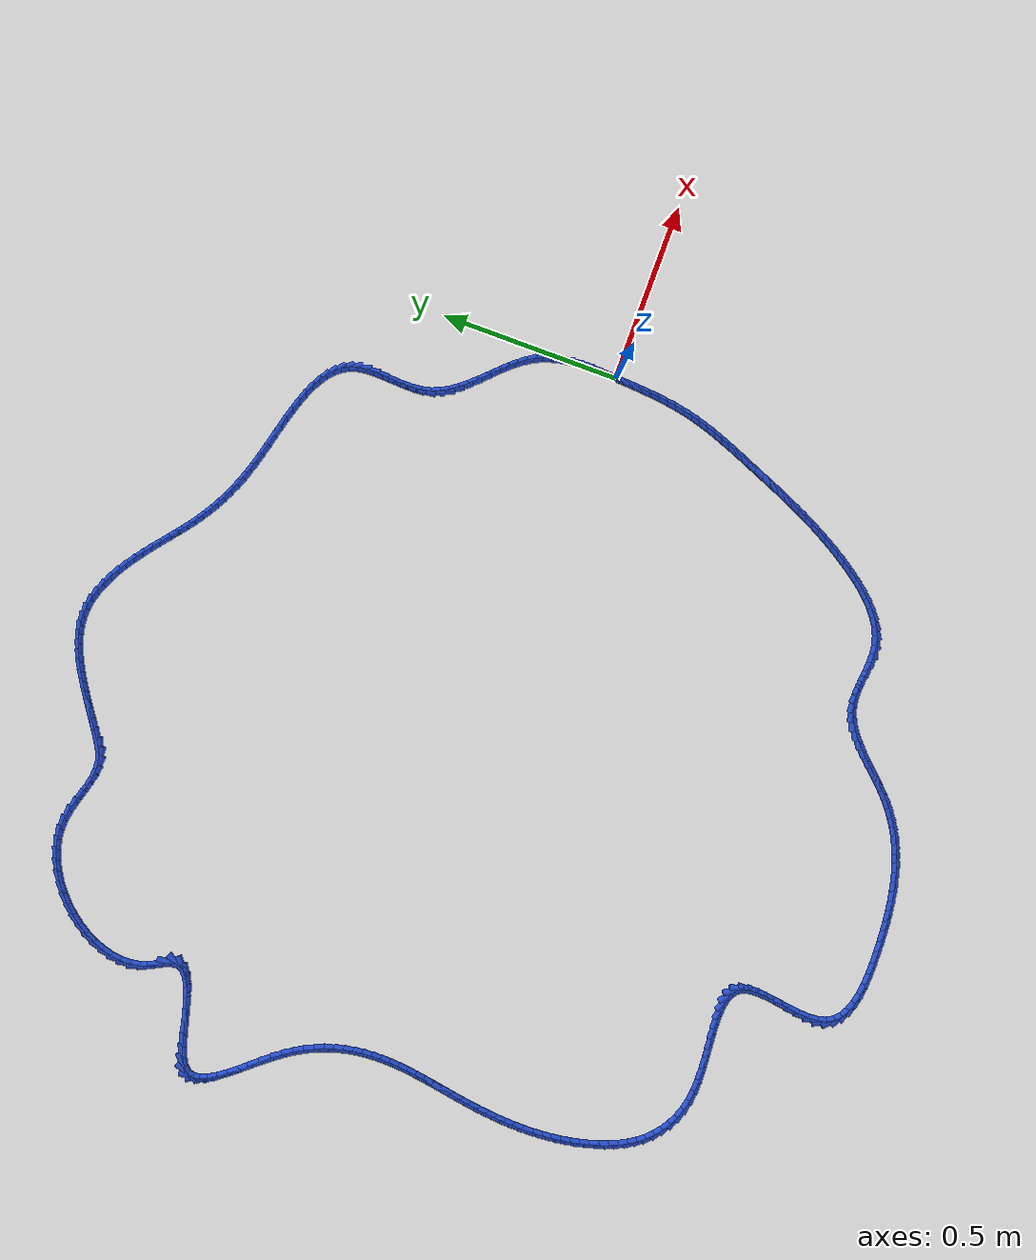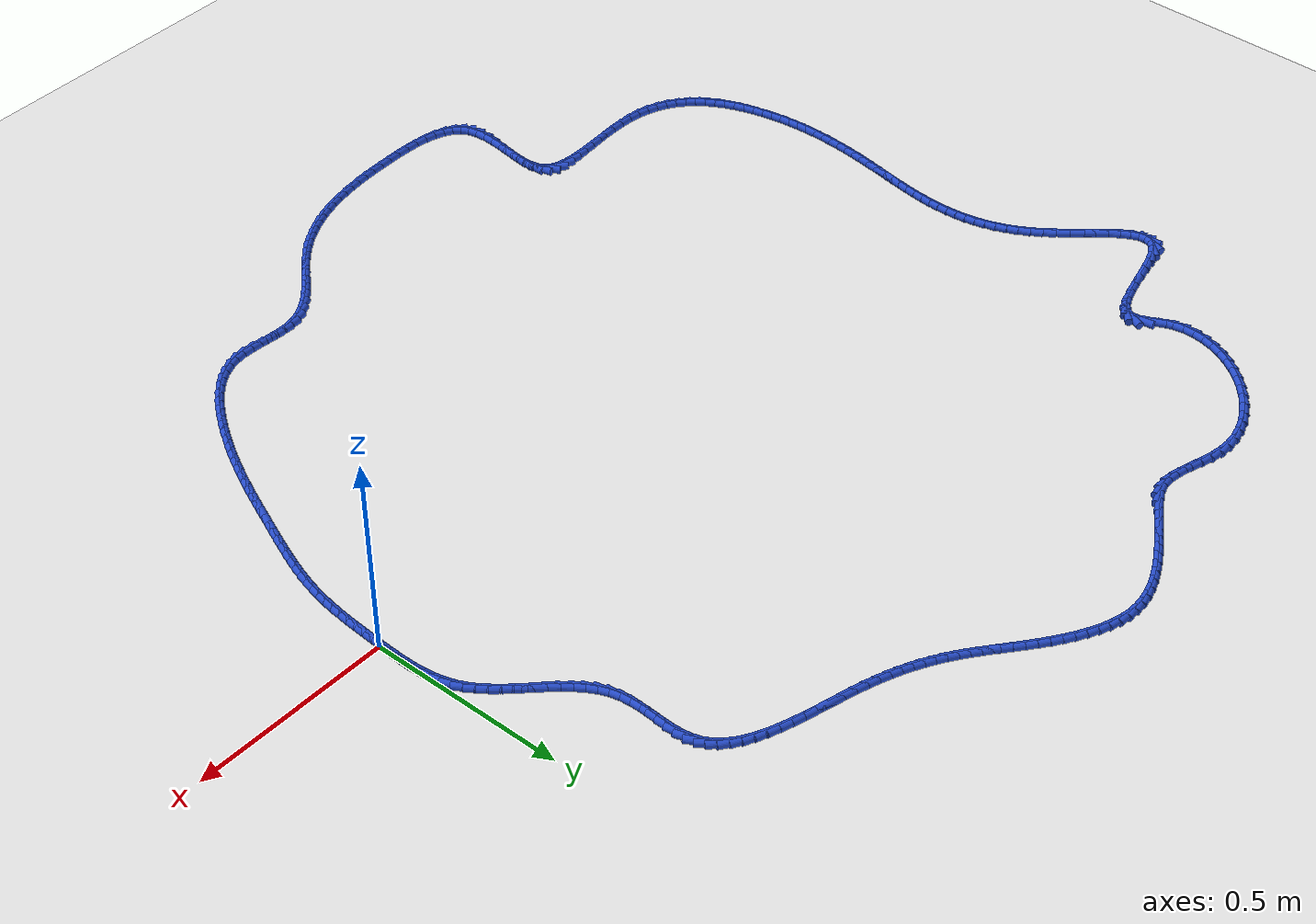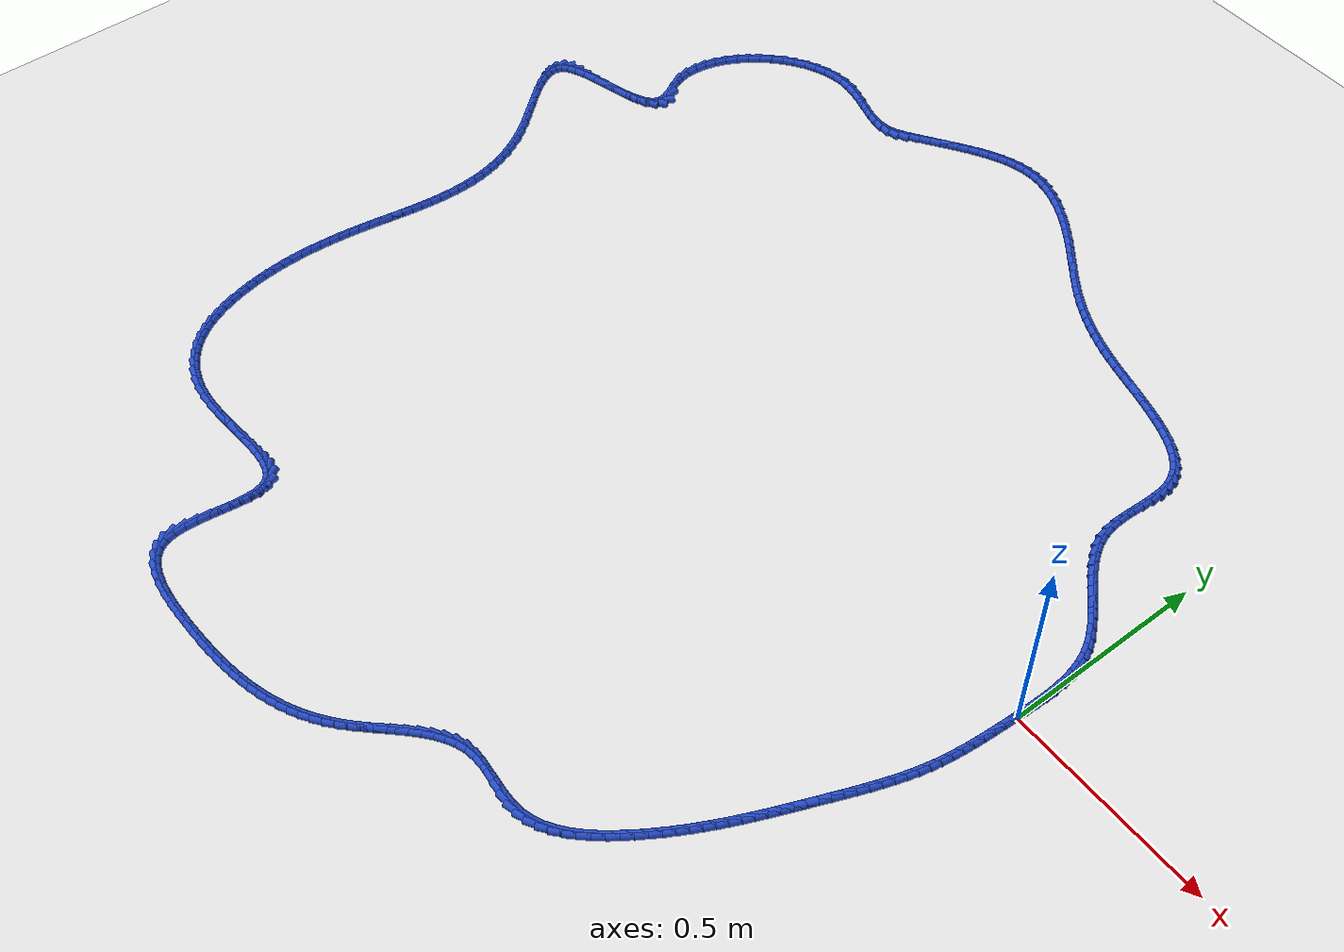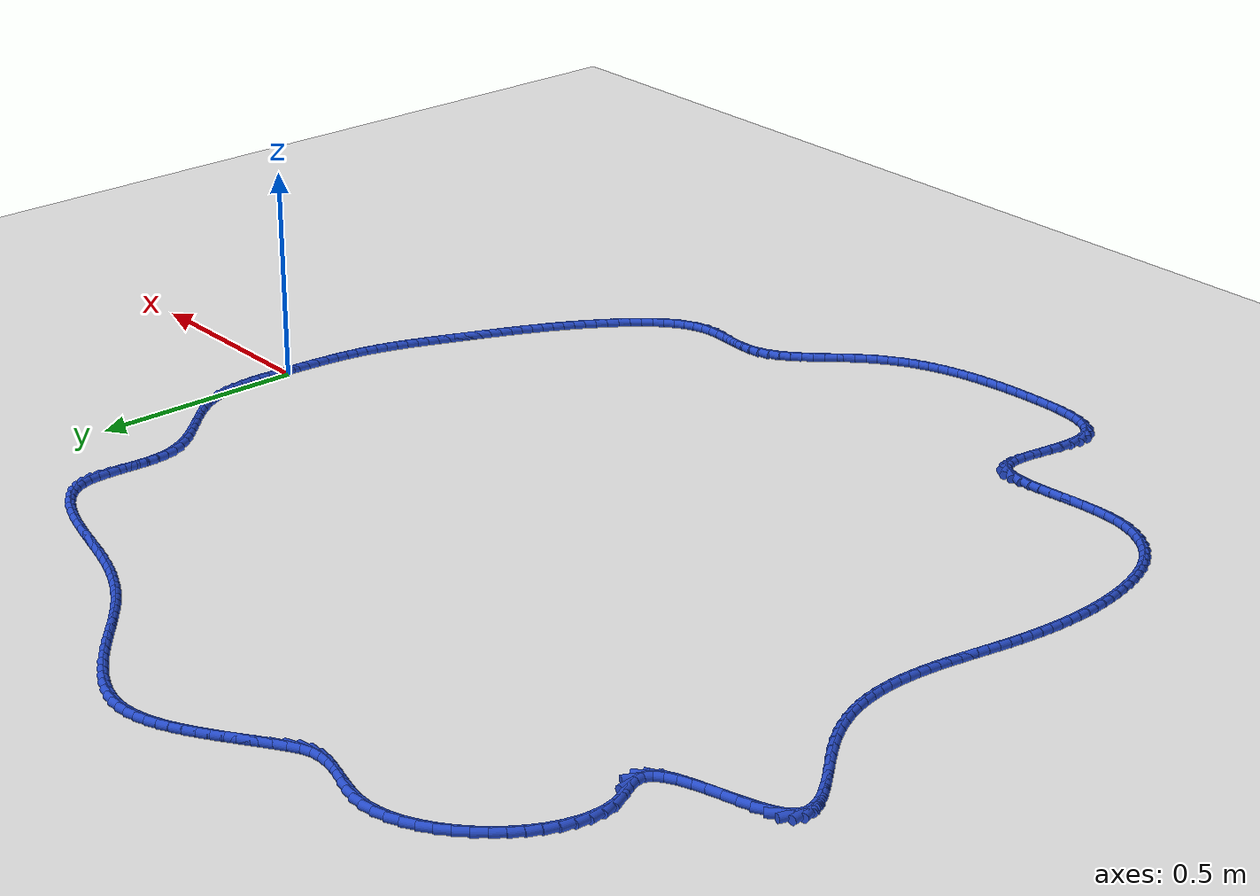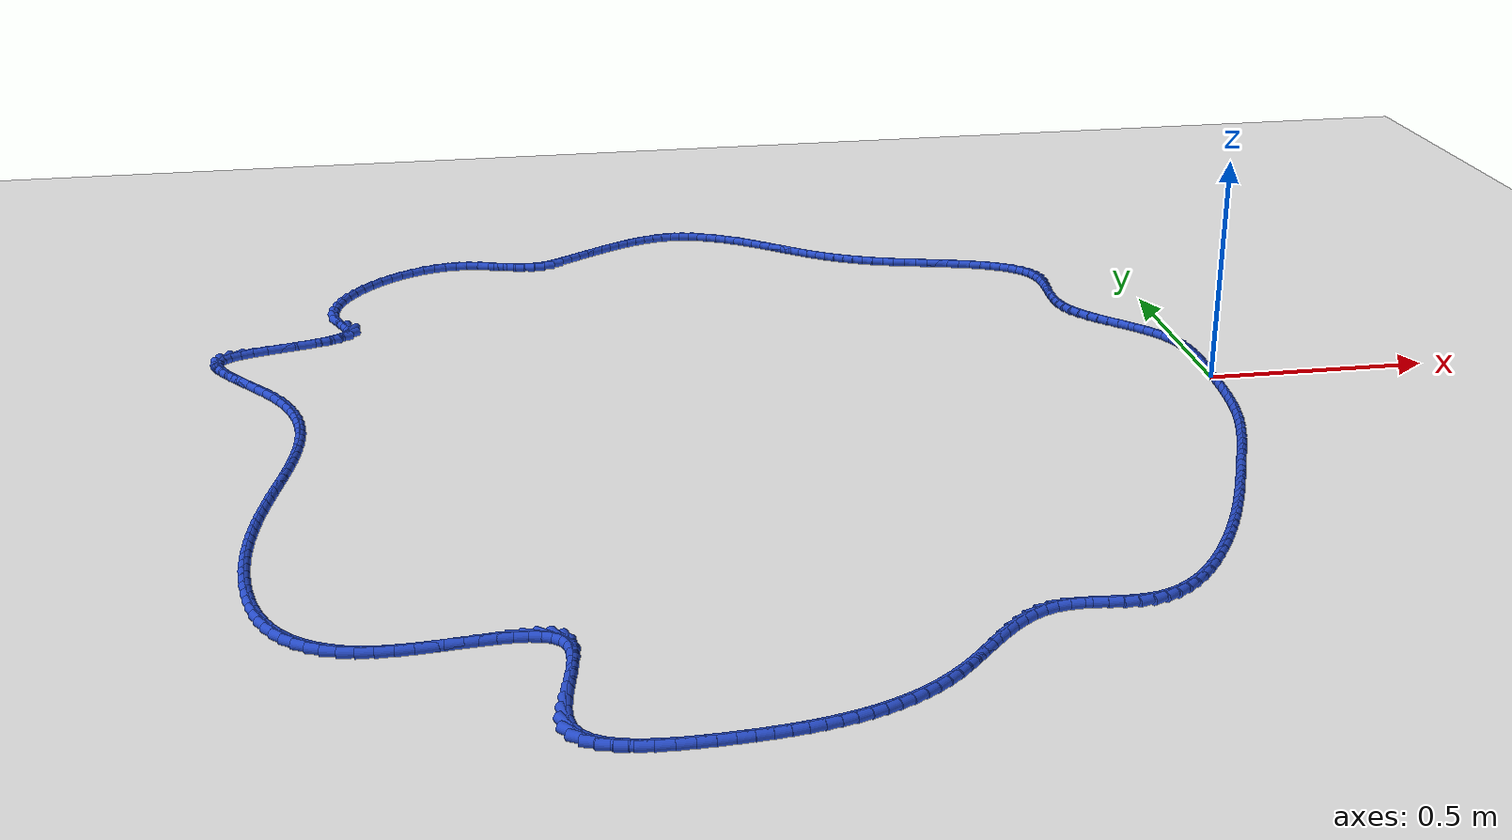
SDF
<sdf version="1.6">
 <world name="default">
  <light name="sun" type="directional">
   <pose>0 0 10 0 -0 0</pose>
   <diffuse>0.8 0.8 0.8 1</diffuse>
   <specular>0.2 0.2 0.2 1</specular>
   <attenuation>
    <range>1000</range>
    <constant>0.9</constant>
    <linear>0.01</linear>
    <quadratic>0.001</quadratic>
   </attenuation>
   <direction>-0.5 0.1 -0.9</direction>
  </light>
  <model name="ground_plane">
   <static>1</static>
   <link name="link">
    <collision name="collision">
     <geometry><plane><normal>0 0 1</normal><size>100 100</size></plane></geometry>
     <surface><friction><ode><mu>100</mu><mu2>50</mu2></ode></friction></surface>
    </collision>
    <visual name="visual">
     <cast_shadows>0</cast_shadows>
     <geometry><plane><normal>0 0 1</normal><size>100 100</size></plane></geometry>
     <material>
      <script><uri>file://media/materials/scripts/gazebo.material</uri><name>Gazebo/WhiteGlow</name></script>
     </material>
    </visual>
   </link>
  </model>
  <gravity>0 0 -9.8</gravity>
  <magnetic_field>6e-06 2.3e-05 -4.2e-05</magnetic_field>
  <atmosphere type="adiabatic"/>
  <physics name="default_physics" default="0" type="ode">
   <max_step_size>0.001</max_step_size>
   <real_time_factor>1</real_time_factor>
   <real_time_update_rate>1000</real_time_update_rate>
  </physics>
  <scene><ambient>0.4 0.4 0.4 1</ambient><background>0.7 0.7 0.7 1</background><shadows>1</shadows></scene>
  <spherical_coordinates>
   <surface_model>EARTH_WGS84</surface_model>
   <latitude_deg>0</latitude_deg>
   <longitude_deg>0</longitude_deg>
   <elevation>0</elevation>
   <heading_deg>0</heading_deg>
  </spherical_coordinates>
  <model name="line">
   <link name="link_0">
    <pose>-2.6020852139652106e-18 1.3877787807814457e-17 0.01 0 1.57 1.5227151973883521</pose>
    <collision name="collision">
     <geometry><cylinder><radius>0.01</radius><length>0.08</length></cylinder></geometry>
    </collision>
    <visual name="visual">
     <material>
      <script><name>Gazebo/Blue</name><uri>file://media/materials/scripts/gazebo.material</uri></script>
     </material>
     <geometry><cylinder><radius>0.01</radius><length>0.08</length></cylinder></geometry>
    </visual>
   </link>
   <link name="link_1">
    <pose>0.00130948528221154 0.027213920630176223 0.01 0 1.57 1.5368727448066788</pose>
    <collision name="collision">
     <geometry><cylinder><radius>0.01</radius><length>0.08</length></cylinder></geometry>
    </collision>
    <visual name="visual">
     <material>
      <script><name>Gazebo/Blue</name><uri>file://media/materials/scripts/gazebo.material</uri></script>
     </material>
     <geometry><cylinder><radius>0.01</radius><length>0.08</length></cylinder></geometry>
    </visual>
   </link>
   <link name="link_2">
    <pose>0.0022365369850442913 0.05453108471755519 0.01 0 1.57 1.5634438854718762</pose>
    <collision name="collision">
     <geometry><cylinder><radius>0.01</radius><length>0.08</length></cylinder></geometry>
    </collision>
    <visual name="visual">
     <material>
      <script><name>Gazebo/Blue</name><uri>file://media/materials/scripts/gazebo.material</uri></script>
     </material>
     <geometry><cylinder><radius>0.01</radius><length>0.08</length></cylinder></geometry>
    </visual>
   </link>
   <link name="link_3">
    <pose>0.0024368110577792333 0.0817697194909264 0.01 0 1.57 -1.5385280119894014</pose>
    <collision name="collision">
     <geometry><cylinder><radius>0.01</radius><length>0.08</length></cylinder></geometry>
    </collision>
    <visual name="visual">
     <material>
      <script><name>Gazebo/Blue</name><uri>file://media/materials/scripts/gazebo.material</uri></script>
     </material>
     <geometry><cylinder><radius>0.01</radius><length>0.08</length></cylinder></geometry>
    </visual>
   </link>
   <link name="link_4">
    <pose>0.0015659634496973463 0.10874805217907922 0.01 0 1.57 -1.484850480481901</pose>
    <collision name="collision">
     <geometry><cylinder><radius>0.01</radius><length>0.08</length></cylinder></geometry>
    </collision>
    <visual name="visual">
     <material>
      <script><name>Gazebo/Blue</name><uri>file://media/materials/scripts/gazebo.material</uri></script>
     </material>
     <geometry><cylinder><radius>0.01</radius><length>0.08</length></cylinder></geometry>
    </visual>
   </link>
   <link name="link_5">
    <pose>-0.0007203498899203851 0.13528431001080327 0.01 0 1.57 -1.4159009603216661</pose>
    <collision name="collision">
     <geometry><cylinder><radius>0.01</radius><length>0.08</length></cylinder></geometry>
    </collision>
    <visual name="visual">
     <material>
      <script><name>Gazebo/Blue</name><uri>file://media/materials/scripts/gazebo.material</uri></script>
     </material>
     <geometry><cylinder><radius>0.01</radius><length>0.08</length></cylinder></geometry>
    </visual>
   </link>
   <link name="link_6">
    <pose>-0.004766473011792985 0.16119672021488798 0.01 0 1.57 -1.3305623658237322</pose>
    <collision name="collision">
     <geometry><cylinder><radius>0.01</radius><length>0.08</length></cylinder></geometry>
    </collision>
    <visual name="visual">
     <material>
      <script><name>Gazebo/Blue</name><uri>file://media/materials/scripts/gazebo.material</uri></script>
     </material>
     <geometry><cylinder><radius>0.01</radius><length>0.08</length></cylinder></geometry>
    </visual>
   </link>
   <link name="link_7">
    <pose>-0.01091674996663946 0.18630351002012288 0.01 0 1.57 -1.2283349155625514</pose>
    <collision name="collision">
     <geometry><cylinder><radius>0.01</radius><length>0.08</length></cylinder></geometry>
    </collision>
    <visual name="visual">
     <material>
      <script><name>Gazebo/Blue</name><uri>file://media/materials/scripts/gazebo.material</uri></script>
     </material>
     <geometry><cylinder><radius>0.01</radius><length>0.08</length></cylinder></geometry>
    </visual>
   </link>
   <link name="link_8">
    <pose>-0.019515524805178843 0.2104229066552974 0.01 0 1.57 -1.110789758326662</pose>
    <collision name="collision">
     <geometry><cylinder><radius>0.01</radius><length>0.08</length></cylinder></geometry>
    </collision>
    <visual name="visual">
     <material>
      <script><name>Gazebo/Blue</name><uri>file://media/materials/scripts/gazebo.material</uri></script>
     </material>
     <geometry><cylinder><radius>0.01</radius><length>0.08</length></cylinder></geometry>
    </visual>
   </link>
   <link name="link_9">
    <pose>-0.030890254631956136 0.2333809655288267 0.01 0 1.57 -0.9987403075591761</pose>
    <collision name="collision">
     <geometry><cylinder><radius>0.01</radius><length>0.08</length></cylinder></geometry>
    </collision>
    <visual name="visual">
     <material>
      <script><name>Gazebo/Blue</name><uri>file://media/materials/scripts/gazebo.material</uri></script>
     </material>
     <geometry><cylinder><radius>0.01</radius><length>0.08</length></cylinder></geometry>
    </visual>
   </link>
   <link name="link_10">
    <pose>-0.04494034271433664 0.2552021723806003 0.01 0 1.57 -0.9126209751661333</pose>
    <collision name="collision">
     <geometry><cylinder><radius>0.01</radius><length>0.08</length></cylinder></geometry>
    </collision>
    <visual name="visual">
     <material>
      <script><name>Gazebo/Blue</name><uri>file://media/materials/scripts/gazebo.material</uri></script>
     </material>
     <geometry><cylinder><radius>0.01</radius><length>0.08</length></cylinder></geometry>
    </visual>
   </link>
   <link name="link_11">
    <pose>-0.061113875863956175 0.2761202269935363 0.01 0 1.57 -0.8520430432106814</pose>
    <collision name="collision">
     <geometry><cylinder><radius>0.01</radius><length>0.08</length></cylinder></geometry>
    </collision>
    <visual name="visual">
     <material>
      <script><name>Gazebo/Blue</name><uri>file://media/materials/scripts/gazebo.material</uri></script>
     </material>
     <geometry><cylinder><radius>0.01</radius><length>0.08</length></cylinder></geometry>
    </visual>
   </link>
   <link name="link_12">
    <pose>-0.07883739733771278 0.29637881596608007 0.01 0 1.57 -0.815038468041573</pose>
    <collision name="collision">
     <geometry><cylinder><radius>0.01</radius><length>0.08</length></cylinder></geometry>
    </collision>
    <visual name="visual">
     <material>
      <script><name>Gazebo/Blue</name><uri>file://media/materials/scripts/gazebo.material</uri></script>
     </material>
     <geometry><cylinder><radius>0.01</radius><length>0.08</length></cylinder></geometry>
    </visual>
   </link>
   <link name="link_13">
    <pose>-0.09753745039250451 0.31622162589667735 0.01 0 1.57 -0.8000355833414103</pose>
    <collision name="collision">
     <geometry><cylinder><radius>0.01</radius><length>0.08</length></cylinder></geometry>
    </collision>
    <visual name="visual">
     <material>
      <script><name>Gazebo/Blue</name><uri>file://media/materials/scripts/gazebo.material</uri></script>
     </material>
     <geometry><cylinder><radius>0.01</radius><length>0.08</length></cylinder></geometry>
    </visual>
   </link>
   <link name="link_14">
    <pose>-0.1166405782852293 0.33589234338377333 0.01 0 1.57 -0.8063276071482272</pose>
    <collision name="collision">
     <geometry><cylinder><radius>0.01</radius><length>0.08</length></cylinder></geometry>
    </collision>
    <visual name="visual">
     <material>
      <script><name>Gazebo/Blue</name><uri>file://media/materials/scripts/gazebo.material</uri></script>
     </material>
     <geometry><cylinder><radius>0.01</radius><length>0.08</length></cylinder></geometry>
    </visual>
   </link>
   <link name="link_15">
    <pose>-0.13557332427278532 0.35563465502581404 0.01 0 1.57 -0.8342183226331656</pose>
    <collision name="collision">
     <geometry><cylinder><radius>0.01</radius><length>0.08</length></cylinder></geometry>
    </collision>
    <visual name="visual">
     <material>
      <script><name>Gazebo/Blue</name><uri>file://media/materials/scripts/gazebo.material</uri></script>
     </material>
     <geometry><cylinder><radius>0.01</radius><length>0.08</length></cylinder></geometry>
    </visual>
   </link>
   <link name="link_16">
    <pose>-0.15376223161207062 0.3756922474212447 0.01 0 1.57 -0.8849646210219787</pose>
    <collision name="collision">
     <geometry><cylinder><radius>0.01</radius><length>0.08</length></cylinder></geometry>
    </collision>
    <visual name="visual">
     <material>
      <script><name>Gazebo/Blue</name><uri>file://media/materials/scripts/gazebo.material</uri></script>
     </material>
     <geometry><cylinder><radius>0.01</radius><length>0.08</length></cylinder></geometry>
    </visual>
   </link>
   <link name="link_17">
    <pose>-0.17063384355998318 0.3963088071685109 0.01 0 1.57 -0.9604649542369275</pose>
    <collision name="collision">
     <geometry><cylinder><radius>0.01</radius><length>0.08</length></cylinder></geometry>
    </collision>
    <visual name="visual">
     <material>
      <script><name>Gazebo/Blue</name><uri>file://media/materials/scripts/gazebo.material</uri></script>
     </material>
     <geometry><cylinder><radius>0.01</radius><length>0.08</length></cylinder></geometry>
    </visual>
   </link>
   <link name="link_18">
    <pose>-0.18561470337342095 0.417728020866058 0.01 0 1.57 -1.0624813587259974</pose>
    <collision name="collision">
     <geometry><cylinder><radius>0.01</radius><length>0.08</length></cylinder></geometry>
    </collision>
    <visual name="visual">
     <material>
      <script><name>Gazebo/Blue</name><uri>file://media/materials/scripts/gazebo.material</uri></script>
     </material>
     <geometry><cylinder><radius>0.01</radius><length>0.08</length></cylinder></geometry>
    </visual>
   </link>
   <link name="link_19">
    <pose>-0.19813135430928216 0.44019357511233187 0.01 0 1.57 -1.191133856044571</pose>
    <collision name="collision">
     <geometry><cylinder><radius>0.01</radius><length>0.08</length></cylinder></geometry>
    </collision>
    <visual name="visual">
     <material>
      <script><name>Gazebo/Blue</name><uri>file://media/materials/scripts/gazebo.material</uri></script>
     </material>
     <geometry><cylinder><radius>0.01</radius><length>0.08</length></cylinder></geometry>
    </visual>
   </link>
   <link name="link_20">
    <pose>-0.20761033962446473 0.46394915650577795 0.01 0 1.57 -1.3408098253370637</pose>
    <collision name="collision">
     <geometry><cylinder><radius>0.01</radius><length>0.08</length></cylinder></geometry>
    </collision>
    <visual name="visual">
     <material>
      <script><name>Gazebo/Blue</name><uri>file://media/materials/scripts/gazebo.material</uri></script>
     </material>
     <geometry><cylinder><radius>0.01</radius><length>0.08</length></cylinder></geometry>
    </visual>
   </link>
   <link name="link_21">
    <pose>-0.21352588659143334 0.48921532959179437 0.01 0 1.57 -1.4718573937363735</pose>
    <collision name="collision">
     <geometry><cylinder><radius>0.01</radius><length>0.08</length></cylinder></geometry>
    </collision>
    <visual name="visual">
     <material>
      <script><name>Gazebo/Blue</name><uri>file://media/materials/scripts/gazebo.material</uri></script>
     </material>
     <geometry><cylinder><radius>0.01</radius><length>0.08</length></cylinder></geometry>
    </visual>
   </link>
   <link name="link_22">
    <pose>-0.21616652865502825 0.5158178005908122 0.01 0 1.57 -1.5585108084027472</pose>
    <collision name="collision">
     <geometry><cylinder><radius>0.01</radius><length>0.08</length></cylinder></geometry>
    </collision>
    <visual name="visual">
     <material>
      <script><name>Gazebo/Blue</name><uri>file://media/materials/scripts/gazebo.material</uri></script>
     </material>
     <geometry><cylinder><radius>0.01</radius><length>0.08</length></cylinder></geometry>
    </visual>
   </link>
   <link name="link_23">
    <pose>-0.21650357908090703 0.54325119473 0.01 0 1.57 1.5357061955538158</pose>
    <collision name="collision">
     <geometry><cylinder><radius>0.01</radius><length>0.08</length></cylinder></geometry>
    </collision>
    <visual name="visual">
     <material>
      <script><name>Gazebo/Blue</name><uri>file://media/materials/scripts/gazebo.material</uri></script>
     </material>
     <geometry><cylinder><radius>0.01</radius><length>0.08</length></cylinder></geometry>
    </visual>
   </link>
   <link name="link_24">
    <pose>-0.21552947370752712 0.5709998948682413 0.01 0 1.57 1.523901479338909</pose>
    <collision name="collision">
     <geometry><cylinder><radius>0.01</radius><length>0.08</length></cylinder></geometry>
    </collision>
    <visual name="visual">
     <material>
      <script><name>Gazebo/Blue</name><uri>file://media/materials/scripts/gazebo.material</uri></script>
     </material>
     <geometry><cylinder><radius>0.01</radius><length>0.08</length></cylinder></geometry>
    </visual>
   </link>
   <link name="link_25">
    <pose>-0.21423664837334586 0.5985482838644194 0.01 0 1.57 1.5477272675293001</pose>
    <collision name="collision">
     <geometry><cylinder><radius>0.01</radius><length>0.08</length></cylinder></geometry>
    </collision>
    <visual name="visual">
     <material>
      <script><name>Gazebo/Blue</name><uri>file://media/materials/scripts/gazebo.material</uri></script>
     </material>
     <geometry><cylinder><radius>0.01</radius><length>0.08</length></cylinder></geometry>
    </visual>
   </link>
   <link name="link_26">
    <pose>-0.21361753891682042 0.6253807445774175 0.01 0 1.57 -1.5299204816164198</pose>
    <collision name="collision">
     <geometry><cylinder><radius>0.01</radius><length>0.08</length></cylinder></geometry>
    </collision>
    <visual name="visual">
     <material>
      <script><name>Gazebo/Blue</name><uri>file://media/materials/scripts/gazebo.material</uri></script>
     </material>
     <geometry><cylinder><radius>0.01</radius><length>0.08</length></cylinder></geometry>
    </visual>
   </link>
   <link name="link_27">
    <pose>-0.21466458117640813 0.6509816598661187 0.01 0 1.57 -1.4166803304599629</pose>
    <collision name="collision">
     <geometry><cylinder><radius>0.01</radius><length>0.08</length></cylinder></geometry>
    </collision>
    <visual name="visual">
     <material>
      <script><name>Gazebo/Blue</name><uri>file://media/materials/scripts/gazebo.material</uri></script>
     </material>
     <geometry><cylinder><radius>0.01</radius><length>0.08</length></cylinder></geometry>
    </visual>
   </link>
   <link name="link_28">
    <pose>-0.21837021099056636 0.6748354125894063 0.01 0 1.57 -1.244981446190736</pose>
    <collision name="collision">
     <geometry><cylinder><radius>0.01</radius><length>0.08</length></cylinder></geometry>
    </collision>
    <visual name="visual">
     <material>
      <script><name>Gazebo/Blue</name><uri>file://media/materials/scripts/gazebo.material</uri></script>
     </material>
     <geometry><cylinder><radius>0.01</radius><length>0.08</length></cylinder></geometry>
    </visual>
   </link>
   <link name="link_29">
    <pose>-0.22567438989955135 0.696454658136865 0.01 0 1.57 -1.0485826543027574</pose>
    <collision name="collision">
     <geometry><cylinder><radius>0.01</radius><length>0.08</length></cylinder></geometry>
    </collision>
    <visual name="visual">
     <material>
      <script><name>Gazebo/Blue</name><uri>file://media/materials/scripts/gazebo.material</uri></script>
     </material>
     <geometry><cylinder><radius>0.01</radius><length>0.08</length></cylinder></geometry>
    </visual>
   </link>
   <link name="link_30">
    <pose>-0.2367788423915427 0.7157498052827794 0.01 0 1.57 -0.8675775483024368</pose>
    <collision name="collision">
     <geometry><cylinder><radius>0.01</radius><length>0.08</length></cylinder></geometry>
    </collision>
    <visual name="visual">
     <material>
      <script><name>Gazebo/Blue</name><uri>file://media/materials/scripts/gazebo.material</uri></script>
     </material>
     <geometry><cylinder><radius>0.01</radius><length>0.08</length></cylinder></geometry>
    </visual>
   </link>
   <link name="link_31">
    <pose>-0.2513400833079454 0.7329250153051418 0.01 0 1.57 -0.7127771329329253</pose>
    <collision name="collision">
     <geometry><cylinder><radius>0.01</radius><length>0.08</length></cylinder></geometry>
    </collision>
    <visual name="visual">
     <material>
      <script><name>Gazebo/Blue</name><uri>file://media/materials/scripts/gazebo.material</uri></script>
     </material>
     <geometry><cylinder><radius>0.01</radius><length>0.08</length></cylinder></geometry>
    </visual>
   </link>
   <link name="link_32">
    <pose>-0.2690018738631253 0.7481913209852199 0.01 0 1.57 -0.5867927093861156</pose>
    <collision name="collision">
     <geometry><cylinder><radius>0.01</radius><length>0.08</length></cylinder></geometry>
    </collision>
    <visual name="visual">
     <material>
      <script><name>Gazebo/Blue</name><uri>file://media/materials/scripts/gazebo.material</uri></script>
     </material>
     <geometry><cylinder><radius>0.01</radius><length>0.08</length></cylinder></geometry>
    </visual>
   </link>
   <link name="link_33">
    <pose>-0.28940797527144874 0.7617597551042825 0.01 0 1.57 -0.48738198558511237</pose>
    <collision name="collision">
     <geometry><cylinder><radius>0.01</radius><length>0.08</length></cylinder></geometry>
    </collision>
    <visual name="visual">
     <material>
      <script><name>Gazebo/Blue</name><uri>file://media/materials/scripts/gazebo.material</uri></script>
     </material>
     <geometry><cylinder><radius>0.01</radius><length>0.08</length></cylinder></geometry>
    </visual>
   </link>
   <link name="link_34">
    <pose>-0.3122021487472816 0.7738413504435968 0.01 0 1.57 -0.41052949769458824</pose>
    <collision name="collision">
     <geometry><cylinder><radius>0.01</radius><length>0.08</length></cylinder></geometry>
    </collision>
    <visual name="visual">
     <material>
      <script><name>Gazebo/Blue</name><uri>file://media/materials/scripts/gazebo.material</uri></script>
     </material>
     <geometry><cylinder><radius>0.01</radius><length>0.08</length></cylinder></geometry>
    </visual>
   </link>
   <link name="link_35">
    <pose>-0.33702815550499 0.7846471397844316 0.01 0 1.57 -0.35223494074170936</pose>
    <collision name="collision">
     <geometry><cylinder><radius>0.01</radius><length>0.08</length></cylinder></geometry>
    </collision>
    <visual name="visual">
     <material>
      <script><name>Gazebo/Blue</name><uri>file://media/materials/scripts/gazebo.material</uri></script>
     </material>
     <geometry><cylinder><radius>0.01</radius><length>0.08</length></cylinder></geometry>
    </visual>
   </link>
   <link name="link_36">
    <pose>-0.3635297567589397 0.7943881559080544 0.01 0 1.57 -0.3091997455386601</pose>
    <collision name="collision">
     <geometry><cylinder><radius>0.01</radius><length>0.08</length></cylinder></geometry>
    </collision>
    <visual name="visual">
     <material>
      <script><name>Gazebo/Blue</name><uri>file://media/materials/scripts/gazebo.material</uri></script>
     </material>
     <geometry><cylinder><radius>0.01</radius><length>0.08</length></cylinder></geometry>
    </visual>
   </link>
   <link name="link_37">
    <pose>-0.39135071372349745 0.8032754315957341 0.01 0 1.57 -0.2789594900883372</pose>
    <collision name="collision">
     <geometry><cylinder><radius>0.01</radius><length>0.08</length></cylinder></geometry>
    </collision>
    <visual name="visual">
     <material>
      <script><name>Gazebo/Blue</name><uri>file://media/materials/scripts/gazebo.material</uri></script>
     </material>
     <geometry><cylinder><radius>0.01</radius><length>0.08</length></cylinder></geometry>
    </visual>
   </link>
   <link name="link_38">
    <pose>-0.42013478761302847 0.8115199996287379 0.01 0 1.57 -0.25981781600576476</pose>
    <collision name="collision">
     <geometry><cylinder><radius>0.01</radius><length>0.08</length></cylinder></geometry>
    </collision>
    <visual name="visual">
     <material>
      <script><name>Gazebo/Blue</name><uri>file://media/materials/scripts/gazebo.material</uri></script>
     </material>
     <geometry><cylinder><radius>0.01</radius><length>0.08</length></cylinder></geometry>
    </visual>
   </link>
   <link name="link_39">
    <pose>-0.4495257396418997 0.8193328927883344 0.01 0 1.57 -0.25074445896426306</pose>
    <collision name="collision">
     <geometry><cylinder><radius>0.01</radius><length>0.08</length></cylinder></geometry>
    </collision>
    <visual name="visual">
     <material>
      <script><name>Gazebo/Blue</name><uri>file://media/materials/scripts/gazebo.material</uri></script>
     </material>
     <geometry><cylinder><radius>0.01</radius><length>0.08</length></cylinder></geometry>
    </visual>
   </link>
   <link name="link_40">
    <pose>-0.4791673310244763 0.8269251438557914 0.01 0 1.57 -0.25129844300568865</pose>
    <collision name="collision">
     <geometry><cylinder><radius>0.01</radius><length>0.08</length></cylinder></geometry>
    </collision>
    <visual name="visual">
     <material>
      <script><name>Gazebo/Blue</name><uri>file://media/materials/scripts/gazebo.material</uri></script>
     </material>
     <geometry><cylinder><radius>0.01</radius><length>0.08</length></cylinder></geometry>
    </visual>
   </link>
   <link name="link_41">
    <pose>-0.508703322975125 0.8345077856123773 0.01 0 1.57 -0.2615962167741072</pose>
    <collision name="collision">
     <geometry><cylinder><radius>0.01</radius><length>0.08</length></cylinder></geometry>
    </collision>
    <visual name="visual">
     <material>
      <script><name>Gazebo/Blue</name><uri>file://media/materials/scripts/gazebo.material</uri></script>
     </material>
     <geometry><cylinder><radius>0.01</radius><length>0.08</length></cylinder></geometry>
    </visual>
   </link>
   <link name="link_42">
    <pose>-0.5377774767082113 0.8422918508393598 0.01 0 1.57 -0.28233117322893336</pose>
    <collision name="collision">
     <geometry><cylinder><radius>0.01</radius><length>0.08</length></cylinder></geometry>
    </collision>
    <visual name="visual">
     <material>
      <script><name>Gazebo/Blue</name><uri>file://media/materials/scripts/gazebo.material</uri></script>
     </material>
     <geometry><cylinder><radius>0.01</radius><length>0.08</length></cylinder></geometry>
    </visual>
   </link>
   <link name="link_43">
    <pose>-0.5660335534381017 0.850488372318007 0.01 0 1.57 -0.31398040004769123</pose>
    <collision name="collision">
     <geometry><cylinder><radius>0.01</radius><length>0.08</length></cylinder></geometry>
    </collision>
    <visual name="visual">
     <material>
      <script><name>Gazebo/Blue</name><uri>file://media/materials/scripts/gazebo.material</uri></script>
     </material>
     <geometry><cylinder><radius>0.01</radius><length>0.08</length></cylinder></geometry>
    </visual>
   </link>
   <link name="link_44">
    <pose>-0.5931509401031935 0.8592939832415143 0.01 0 1.57 -0.3508246991687764</pose>
    <collision name="collision">
     <geometry><cylinder><radius>0.01</radius><length>0.08</length></cylinder></geometry>
    </collision>
    <visual name="visual">
     <material>
      <script><name>Gazebo/Blue</name><uri>file://media/materials/scripts/gazebo.material</uri></script>
     </material>
     <geometry><cylinder><radius>0.01</radius><length>0.08</length></cylinder></geometry>
    </visual>
   </link>
   <link name="link_45">
    <pose>-0.6190965180657434 0.8687891142166171 0.01 0 1.57 -0.3893815449309612</pose>
    <collision name="collision">
     <geometry><cylinder><radius>0.01</radius><length>0.08</length></cylinder></geometry>
    </collision>
    <visual name="visual">
     <material>
      <script><name>Gazebo/Blue</name><uri>file://media/materials/scripts/gazebo.material</uri></script>
     </material>
     <geometry><cylinder><radius>0.01</radius><length>0.08</length></cylinder></geometry>
    </visual>
   </link>
   <link name="link_46">
    <pose>-0.6439761425299153 0.8789980239088264 0.01 0 1.57 -0.42917657582938307</pose>
    <collision name="collision">
     <geometry><cylinder><radius>0.01</radius><length>0.08</length></cylinder></geometry>
    </collision>
    <visual name="visual">
     <material>
      <script><name>Gazebo/Blue</name><uri>file://media/materials/scripts/gazebo.material</uri></script>
     </material>
     <geometry><cylinder><radius>0.01</radius><length>0.08</length></cylinder></geometry>
    </visual>
   </link>
   <link name="link_47">
    <pose>-0.6678965727561397 0.8899446055724728 0.01 0 1.57 -0.4696688643362292</pose>
    <collision name="collision">
     <geometry><cylinder><radius>0.01</radius><length>0.08</length></cylinder></geometry>
    </collision>
    <visual name="visual">
     <material>
      <script><name>Gazebo/Blue</name><uri>file://media/materials/scripts/gazebo.material</uri></script>
     </material>
     <geometry><cylinder><radius>0.01</radius><length>0.08</length></cylinder></geometry>
    </visual>
   </link>
   <link name="link_48">
    <pose>-0.6909645680048476 0.9016527524618874 0.01 0 1.57 -0.5102531969280759</pose>
    <collision name="collision">
     <geometry><cylinder><radius>0.01</radius><length>0.08</length></cylinder></geometry>
    </collision>
    <visual name="visual">
     <material>
      <script><name>Gazebo/Blue</name><uri>file://media/materials/scripts/gazebo.material</uri></script>
     </material>
     <geometry><cylinder><radius>0.01</radius><length>0.08</length></cylinder></geometry>
    </visual>
   </link>
   <link name="link_49">
    <pose>-0.7132868875364696 0.9141463578314011 0.01 0 1.57 -0.5502932231464625</pose>
    <collision name="collision">
     <geometry><cylinder><radius>0.01</radius><length>0.08</length></cylinder></geometry>
    </collision>
    <visual name="visual">
     <material>
      <script><name>Gazebo/Blue</name><uri>file://media/materials/scripts/gazebo.material</uri></script>
     </material>
     <geometry><cylinder><radius>0.01</radius><length>0.08</length></cylinder></geometry>
    </visual>
   </link>
   <link name="link_50">
    <pose>-0.7349702906114366 0.9274493149353447 0.01 0 1.57 -0.5891594653885001</pose>
    <collision name="collision">
     <geometry><cylinder><radius>0.01</radius><length>0.08</length></cylinder></geometry>
    </collision>
    <visual name="visual">
     <material>
      <script><name>Gazebo/Blue</name><uri>file://media/materials/scripts/gazebo.material</uri></script>
     </material>
     <geometry><cylinder><radius>0.01</radius><length>0.08</length></cylinder></geometry>
    </visual>
   </link>
   <link name="link_51">
    <pose>-0.7561215364901788 0.9415855170280488 0.01 0 1.57 -0.6250550696593198</pose>
    <collision name="collision">
     <geometry><cylinder><radius>0.01</radius><length>0.08</length></cylinder></geometry>
    </collision>
    <visual name="visual">
     <material>
      <script><name>Gazebo/Blue</name><uri>file://media/materials/scripts/gazebo.material</uri></script>
     </material>
     <geometry><cylinder><radius>0.01</radius><length>0.08</length></cylinder></geometry>
    </visual>
   </link>
   <link name="link_52">
    <pose>-0.7768531219800193 0.9565447694369497 0.01 0 1.57 -0.6526246134478019</pose>
    <collision name="collision">
     <geometry><cylinder><radius>0.01</radius><length>0.08</length></cylinder></geometry>
    </collision>
    <visual name="visual">
     <material>
      <script><name>Gazebo/Blue</name><uri>file://media/materials/scripts/gazebo.material</uri></script>
     </material>
     <geometry><cylinder><radius>0.01</radius><length>0.08</length></cylinder></geometry>
    </visual>
   </link>
   <link name="link_53">
    <pose>-0.7973014967922487 0.9721745684408953 0.01 0 1.57 -0.670656787979252</pose>
    <collision name="collision">
     <geometry><cylinder><radius>0.01</radius><length>0.08</length></cylinder></geometry>
    </collision>
    <visual name="visual">
     <material>
      <script><name>Gazebo/Blue</name><uri>file://media/materials/scripts/gazebo.material</uri></script>
     </material>
     <geometry><cylinder><radius>0.01</radius><length>0.08</length></cylinder></geometry>
    </visual>
   </link>
   <link name="link_54">
    <pose>-0.817609360399337 0.9882852792231259 0.01 0 1.57 -0.6793457127340718</pose>
    <collision name="collision">
     <geometry><cylinder><radius>0.01</radius><length>0.08</length></cylinder></geometry>
    </collision>
    <visual name="visual">
     <material>
      <script><name>Gazebo/Blue</name><uri>file://media/materials/scripts/gazebo.material</uri></script>
     </material>
     <geometry><cylinder><radius>0.01</radius><length>0.08</length></cylinder></geometry>
    </visual>
   </link>
   <link name="link_55">
    <pose>-0.8379194122910979 1.0046872668638427 0.01 0 1.57 -0.6788908529354363</pose>
    <collision name="collision">
     <geometry><cylinder><radius>0.01</radius><length>0.08</length></cylinder></geometry>
    </collision>
    <visual name="visual">
     <material>
      <script><name>Gazebo/Blue</name><uri>file://media/materials/scripts/gazebo.material</uri></script>
     </material>
     <geometry><cylinder><radius>0.01</radius><length>0.08</length></cylinder></geometry>
    </visual>
   </link>
   <link name="link_56">
    <pose>-0.858374351957344 1.0211908964432463 0.01 0 1.57 -0.6694750202575084</pose>
    <collision name="collision">
     <geometry><cylinder><radius>0.01</radius><length>0.08</length></cylinder></geometry>
    </collision>
    <visual name="visual">
     <material>
      <script><name>Gazebo/Blue</name><uri>file://media/materials/scripts/gazebo.material</uri></script>
     </material>
     <geometry><cylinder><radius>0.01</radius><length>0.08</length></cylinder></geometry>
    </visual>
   </link>
   <link name="link_57">
    <pose>-0.8791168788878889 1.0376065330415372 0.01 0 1.57 -0.6512661873461716</pose>
    <collision name="collision">
     <geometry><cylinder><radius>0.01</radius><length>0.08</length></cylinder></geometry>
    </collision>
    <visual name="visual">
     <material>
      <script><name>Gazebo/Blue</name><uri>file://media/materials/scripts/gazebo.material</uri></script>
     </material>
     <geometry><cylinder><radius>0.01</radius><length>0.08</length></cylinder></geometry>
    </visual>
   </link>
   <link name="link_58">
    <pose>-0.9002896925725462 1.053744541738917 0.01 0 1.57 -0.6244399604506423</pose>
    <collision name="collision">
     <geometry><cylinder><radius>0.01</radius><length>0.08</length></cylinder></geometry>
    </collision>
    <visual name="visual">
     <material>
      <script><name>Gazebo/Blue</name><uri>file://media/materials/scripts/gazebo.material</uri></script>
     </material>
     <geometry><cylinder><radius>0.01</radius><length>0.08</length></cylinder></geometry>
    </visual>
   </link>
   <link name="link_59">
    <pose>-0.9220354925011287 1.0694152876155858 0.01 0 1.57 -0.5892198338551388</pose>
    <collision name="collision">
     <geometry><cylinder><radius>0.01</radius><length>0.08</length></cylinder></geometry>
    </collision>
    <visual name="visual">
     <material>
      <script><name>Gazebo/Blue</name><uri>file://media/materials/scripts/gazebo.material</uri></script>
     </material>
     <geometry><cylinder><radius>0.01</radius><length>0.08</length></cylinder></geometry>
    </visual>
   </link>
   <link name="link_60">
    <pose>-0.9444969781634495 1.0844291357517444 0.01 0 1.57 -0.5458840641427832</pose>
    <collision name="collision">
     <geometry><cylinder><radius>0.01</radius><length>0.08</length></cylinder></geometry>
    </collision>
    <visual name="visual">
     <material>
      <script><name>Gazebo/Blue</name><uri>file://media/materials/scripts/gazebo.material</uri></script>
     </material>
     <geometry><cylinder><radius>0.01</radius><length>0.08</length></cylinder></geometry>
    </visual>
   </link>
   <link name="link_61">
    <pose>-0.9677831875895506 1.098574491032894 0.01 0 1.57 -0.4939353453942742</pose>
    <collision name="collision">
     <geometry><cylinder><radius>0.01</radius><length>0.08</length></cylinder></geometry>
    </collision>
    <visual name="visual">
     <material>
      <script><name>Gazebo/Blue</name><uri>file://media/materials/scripts/gazebo.material</uri></script>
     </material>
     <geometry><cylinder><radius>0.01</radius><length>0.08</length></cylinder></geometry>
    </visual>
   </link>
   <link name="link_62">
    <pose>-0.9917930955604587 1.11150271646106 0.01 0 1.57 -0.4316734780079301</pose>
    <collision name="collision">
     <geometry><cylinder><radius>0.01</radius><length>0.08</length></cylinder></geometry>
    </collision>
    <visual name="visual">
     <material>
      <script><name>Gazebo/Blue</name><uri>file://media/materials/scripts/gazebo.material</uri></script>
     </material>
     <geometry><cylinder><radius>0.01</radius><length>0.08</length></cylinder></geometry>
    </visual>
   </link>
   <link name="link_63">
    <pose>-1.0163447941989177 1.1228124084935085 0.01 0 1.57 -0.3569346080916648</pose>
    <collision name="collision">
     <geometry><cylinder><radius>0.01</radius><length>0.08</length></cylinder></geometry>
    </collision>
    <visual name="visual">
     <material>
      <script><name>Gazebo/Blue</name><uri>file://media/materials/scripts/gazebo.material</uri></script>
     </material>
     <geometry><cylinder><radius>0.01</radius><length>0.08</length></cylinder></geometry>
    </visual>
   </link>
   <link name="link_64">
    <pose>-1.0412562056329908 1.1321020526857102 0.01 0 1.57 -0.26720207361551657</pose>
    <collision name="collision">
     <geometry><cylinder><radius>0.01</radius><length>0.08</length></cylinder></geometry>
    </collision>
    <visual name="visual">
     <material>
      <script><name>Gazebo/Blue</name><uri>file://media/materials/scripts/gazebo.material</uri></script>
     </material>
     <geometry><cylinder><radius>0.01</radius><length>0.08</length></cylinder></geometry>
    </visual>
   </link>
   <link name="link_65">
    <pose>-1.0663452519907428 1.1389701345931373 0.01 0 1.57 -0.15987820856925658</pose>
    <collision name="collision">
     <geometry><cylinder><radius>0.01</radius><length>0.08</length></cylinder></geometry>
    </collision>
    <visual name="visual">
     <material>
      <script><name>Gazebo/Blue</name><uri>file://media/materials/scripts/gazebo.material</uri></script>
     </material>
     <geometry><cylinder><radius>0.01</radius><length>0.08</length></cylinder></geometry>
    </visual>
   </link>
   <link name="link_66">
    <pose>-1.0914298554002373 1.1430151397712618 0.01 0 1.57 -0.035366285686373206</pose>
    <collision name="collision">
     <geometry><cylinder><radius>0.01</radius><length>0.08</length></cylinder></geometry>
    </collision>
    <visual name="visual">
     <material>
      <script><name>Gazebo/Blue</name><uri>file://media/materials/scripts/gazebo.material</uri></script>
     </material>
     <geometry><cylinder><radius>0.01</radius><length>0.08</length></cylinder></geometry>
    </visual>
   </link>
   <link name="link_67">
    <pose>-1.1163445619069452 1.1438966479525723 0.01 0 1.57 0.08777751779489701</pose>
    <collision name="collision">
     <geometry><cylinder><radius>0.01</radius><length>0.08</length></cylinder></geometry>
    </collision>
    <visual name="visual">
     <material>
      <script><name>Gazebo/Blue</name><uri>file://media/materials/scripts/gazebo.material</uri></script>
     </material>
     <geometry><cylinder><radius>0.01</radius><length>0.08</length></cylinder></geometry>
    </visual>
   </link>
   <link name="link_68">
    <pose>-1.1410459813712508 1.141722832791979 0.01 0 1.57 0.19822811877074115</pose>
    <collision name="collision">
     <geometry><cylinder><radius>0.01</radius><length>0.08</length></cylinder></geometry>
    </collision>
    <visual name="visual">
     <material>
      <script><name>Gazebo/Blue</name><uri>file://media/materials/scripts/gazebo.material</uri></script>
     </material>
     <geometry><cylinder><radius>0.01</radius><length>0.08</length></cylinder></geometry>
    </visual>
   </link>
   <link name="link_69">
    <pose>-1.1655451225710551 1.1368017881566346 0.01 0 1.57 0.2939769712846466</pose>
    <collision name="collision">
     <geometry><cylinder><radius>0.01</radius><length>0.08</length></cylinder></geometry>
    </collision>
    <visual name="visual">
     <material>
      <script><name>Gazebo/Blue</name><uri>file://media/materials/scripts/gazebo.material</uri></script>
     </material>
     <geometry><cylinder><radius>0.01</radius><length>0.08</length></cylinder></geometry>
    </visual>
   </link>
   <link name="link_70">
    <pose>-1.1898532442997742 1.1294425267399657 0.01 0 1.57 0.37467345407495184</pose>
    <collision name="collision">
     <geometry><cylinder><radius>0.01</radius><length>0.08</length></cylinder></geometry>
    </collision>
    <visual name="visual">
     <material>
      <script><name>Gazebo/Blue</name><uri>file://media/materials/scripts/gazebo.material</uri></script>
     </material>
     <geometry><cylinder><radius>0.01</radius><length>0.08</length></cylinder></geometry>
    </visual>
   </link>
   <link name="link_71">
    <pose>-1.213981605350824 1.1199540612354015 0.01 0 1.57 0.4409842234390131</pose>
    <collision name="collision">
     <geometry><cylinder><radius>0.01</radius><length>0.08</length></cylinder></geometry>
    </collision>
    <visual name="visual">
     <material>
      <script><name>Gazebo/Blue</name><uri>file://media/materials/scripts/gazebo.material</uri></script>
     </material>
     <geometry><cylinder><radius>0.01</radius><length>0.08</length></cylinder></geometry>
    </visual>
   </link>
   <link name="link_72">
    <pose>-1.23794146451762 1.1086454043363694 0.01 0 1.57 0.4940404494765025</pose>
    <collision name="collision">
     <geometry><cylinder><radius>0.01</radius><length>0.08</length></cylinder></geometry>
    </collision>
    <visual name="visual">
     <material>
      <script><name>Gazebo/Blue</name><uri>file://media/materials/scripts/gazebo.material</uri></script>
     </material>
     <geometry><cylinder><radius>0.01</radius><length>0.08</length></cylinder></geometry>
    </visual>
   </link>
   <link name="link_73">
    <pose>-1.261744080593579 1.0958255687362972 0.01 0 1.57 0.535056958710037</pose>
    <collision name="collision">
     <geometry><cylinder><radius>0.01</radius><length>0.08</length></cylinder></geometry>
    </collision>
    <visual name="visual">
     <material>
      <script><name>Gazebo/Blue</name><uri>file://media/materials/scripts/gazebo.material</uri></script>
     </material>
     <geometry><cylinder><radius>0.01</radius><length>0.08</length></cylinder></geometry>
    </visual>
   </link>
   <link name="link_74">
    <pose>-1.2854007123721158 1.0818035671286133 0.01 0 1.57 0.5651137857989061</pose>
    <collision name="collision">
     <geometry><cylinder><radius>0.01</radius><length>0.08</length></cylinder></geometry>
    </collision>
    <visual name="visual">
     <material>
      <script><name>Gazebo/Blue</name><uri>file://media/materials/scripts/gazebo.material</uri></script>
     </material>
     <geometry><cylinder><radius>0.01</radius><length>0.08</length></cylinder></geometry>
    </visual>
   </link>
   <link name="link_75">
    <pose>-1.3089226186466474 1.0668884122067457 0.01 0 1.57 0.5850479629905182</pose>
    <collision name="collision">
     <geometry><cylinder><radius>0.01</radius><length>0.08</length></cylinder></geometry>
    </collision>
    <visual name="visual">
     <material>
      <script><name>Gazebo/Blue</name><uri>file://media/materials/scripts/gazebo.material</uri></script>
     </material>
     <geometry><cylinder><radius>0.01</radius><length>0.08</length></cylinder></geometry>
    </visual>
   </link>
   <link name="link_76">
    <pose>-1.332321058210589 1.051389116664122 0.01 0 1.57 0.5954063270164329</pose>
    <collision name="collision">
     <geometry><cylinder><radius>0.01</radius><length>0.08</length></cylinder></geometry>
    </collision>
    <visual name="visual">
     <material>
      <script><name>Gazebo/Blue</name><uri>file://media/materials/scripts/gazebo.material</uri></script>
     </material>
     <geometry><cylinder><radius>0.01</radius><length>0.08</length></cylinder></geometry>
    </visual>
   </link>
   <link name="link_77">
    <pose>-1.3556072898573572 1.0356146931941712 0.01 0 1.57 0.596425573063841</pose>
    <collision name="collision">
     <geometry><cylinder><radius>0.01</radius><length>0.08</length></cylinder></geometry>
    </collision>
    <visual name="visual">
     <material>
      <script><name>Gazebo/Blue</name><uri>file://media/materials/scripts/gazebo.material</uri></script>
     </material>
     <geometry><cylinder><radius>0.01</radius><length>0.08</length></cylinder></geometry>
    </visual>
   </link>
   <link name="link_78">
    <pose>-1.3787925723803678 1.0198741544903198 0.01 0 1.57 0.5880199827626478</pose>
    <collision name="collision">
     <geometry><cylinder><radius>0.01</radius><length>0.08</length></cylinder></geometry>
    </collision>
    <visual name="visual">
     <material>
      <script><name>Gazebo/Blue</name><uri>file://media/materials/scripts/gazebo.material</uri></script>
     </material>
     <geometry><cylinder><radius>0.01</radius><length>0.08</length></cylinder></geometry>
    </visual>
   </link>
   <link name="link_79">
    <pose>-1.4018881645730366 1.0044765132459972 0.01 0 1.57 0.5697676212457384</pose>
    <collision name="collision">
     <geometry><cylinder><radius>0.01</radius><length>0.08</length></cylinder></geometry>
    </collision>
    <visual name="visual">
     <material>
      <script><name>Gazebo/Blue</name><uri>file://media/materials/scripts/gazebo.material</uri></script>
     </material>
     <geometry><cylinder><radius>0.01</radius><length>0.08</length></cylinder></geometry>
    </visual>
   </link>
   <link name="link_80">
    <pose>-1.4249053252287789 0.9897307821546306 0.01 0 1.57 0.518687345700134</pose>
    <collision name="collision">
     <geometry><cylinder><radius>0.01</radius><length>0.08</length></cylinder></geometry>
    </collision>
    <visual name="visual">
     <material>
      <script><name>Gazebo/Blue</name><uri>file://media/materials/scripts/gazebo.material</uri></script>
     </material>
     <geometry><cylinder><radius>0.01</radius><length>0.08</length></cylinder></geometry>
    </visual>
   </link>
   <link name="link_81">
    <pose>-1.4479512978194276 0.976575676384733 0.01 0 1.57 0.328963398376115</pose>
    <collision name="collision">
     <geometry><cylinder><radius>0.01</radius><length>0.08</length></cylinder></geometry>
    </collision>
    <visual name="visual">
     <material>
      <script><name>Gazebo/Blue</name><uri>file://media/materials/scripts/gazebo.material</uri></script>
     </material>
     <geometry><cylinder><radius>0.01</radius><length>0.08</length></cylinder></geometry>
    </visual>
   </link>
   <link name="link_82">
    <pose>-1.4715387472456862 0.9685236981429537 0.01 0 1.57 0.09422918050708343</pose>
    <collision name="collision">
     <geometry><cylinder><radius>0.01</radius><length>0.08</length></cylinder></geometry>
    </collision>
    <visual name="visual">
     <material>
      <script><name>Gazebo/Blue</name><uri>file://media/materials/scripts/gazebo.material</uri></script>
     </material>
     <geometry><cylinder><radius>0.01</radius><length>0.08</length></cylinder></geometry>
    </visual>
   </link>
   <link name="link_83">
    <pose>-1.49585915958344 0.9662251986901429 0.01 0 1.57 -0.08604895369260444</pose>
    <collision name="collision">
     <geometry><cylinder><radius>0.01</radius><length>0.08</length></cylinder></geometry>
    </collision>
    <visual name="visual">
     <material>
      <script><name>Gazebo/Blue</name><uri>file://media/materials/scripts/gazebo.material</uri></script>
     </material>
     <geometry><cylinder><radius>0.01</radius><length>0.08</length></cylinder></geometry>
    </visual>
   </link>
   <link name="link_84">
    <pose>-1.5208667822480049 0.9683824053746972 0.01 0 1.57 -0.2037302960191665</pose>
    <collision name="collision">
     <geometry><cylinder><radius>0.01</radius><length>0.08</length></cylinder></geometry>
    </collision>
    <visual name="visual">
     <material>
      <script><name>Gazebo/Blue</name><uri>file://media/materials/scripts/gazebo.material</uri></script>
     </material>
     <geometry><cylinder><radius>0.01</radius><length>0.08</length></cylinder></geometry>
    </visual>
   </link>
   <link name="link_85">
    <pose>-1.546513847878247 0.9736810011993966 0.01 0 1.57 -0.265175040987169</pose>
    <collision name="collision">
     <geometry><cylinder><radius>0.01</radius><length>0.08</length></cylinder></geometry>
    </collision>
    <visual name="visual">
     <material>
      <script><name>Gazebo/Blue</name><uri>file://media/materials/scripts/gazebo.material</uri></script>
     </material>
     <geometry><cylinder><radius>0.01</radius><length>0.08</length></cylinder></geometry>
    </visual>
   </link>
   <link name="link_86">
    <pose>-1.5727525891130314 0.9808066691670201 0.01 0 1.57 -0.27782451920922663</pose>
    <collision name="collision">
     <geometry><cylinder><radius>0.01</radius><length>0.08</length></cylinder></geometry>
    </collision>
    <visual name="visual">
     <material>
      <script><name>Gazebo/Blue</name><uri>file://media/materials/scripts/gazebo.material</uri></script>
     </material>
     <geometry><cylinder><radius>0.01</radius><length>0.08</length></cylinder></geometry>
    </visual>
   </link>
   <link name="link_87">
    <pose>-1.5995352385912252 0.988445092280348 0.01 0 1.57 -0.24557075869494568</pose>
    <collision name="collision">
     <geometry><cylinder><radius>0.01</radius><length>0.08</length></cylinder></geometry>
    </collision>
    <visual name="visual">
     <material>
      <script><name>Gazebo/Blue</name><uri>file://media/materials/scripts/gazebo.material</uri></script>
     </material>
     <geometry><cylinder><radius>0.01</radius><length>0.08</length></cylinder></geometry>
    </visual>
   </link>
   <link name="link_88">
    <pose>-1.6268140289516935 0.9952819535421591 0.01 0 1.57 -0.1686482932324853</pose>
    <collision name="collision">
     <geometry><cylinder><radius>0.01</radius><length>0.08</length></cylinder></geometry>
    </collision>
    <visual name="visual">
     <material>
      <script><name>Gazebo/Blue</name><uri>file://media/materials/scripts/gazebo.material</uri></script>
     </material>
     <geometry><cylinder><radius>0.01</radius><length>0.08</length></cylinder></geometry>
    </visual>
   </link>
   <link name="link_89">
    <pose>-1.654541192833302 1.0000029359552334 0.01 0 1.57 -0.04618059004545107</pose>
    <collision name="collision">
     <geometry><cylinder><radius>0.01</radius><length>0.08</length></cylinder></geometry>
    </collision>
    <visual name="visual">
     <material>
      <script><name>Gazebo/Blue</name><uri>file://media/materials/scripts/gazebo.material</uri></script>
     </material>
     <geometry><cylinder><radius>0.01</radius><length>0.08</length></cylinder></geometry>
    </visual>
   </link>
   <link name="link_90">
    <pose>-1.6826675076257382 1.0013027499142875 0.01 0 1.57 0.09954961130455764</pose>
    <collision name="collision">
     <geometry><cylinder><radius>0.01</radius><length>0.08</length></cylinder></geometry>
    </collision>
    <visual name="visual">
     <material>
      <script><name>Gazebo/Blue</name><uri>file://media/materials/scripts/gazebo.material</uri></script>
     </material>
     <geometry><cylinder><radius>0.01</radius><length>0.08</length></cylinder></geometry>
    </visual>
   </link>
   <link name="link_91">
    <pose>-1.71104832216541 0.9984680806904148 0.01 0 1.57 0.2333295992190339</pose>
    <collision name="collision">
     <geometry><cylinder><radius>0.01</radius><length>0.08</length></cylinder></geometry>
    </collision>
    <visual name="visual">
     <material>
      <script><name>Gazebo/Blue</name><uri>file://media/materials/scripts/gazebo.material</uri></script>
     </material>
     <geometry><cylinder><radius>0.01</radius><length>0.08</length></cylinder></geometry>
    </visual>
   </link>
   <link name="link_92">
    <pose>-1.739386206889711 0.9917333484910373 0.01 0 1.57 0.3531602088894191</pose>
    <collision name="collision">
     <geometry><cylinder><radius>0.01</radius><length>0.08</length></cylinder></geometry>
    </collision>
    <visual name="visual">
     <material>
      <script><name>Gazebo/Blue</name><uri>file://media/materials/scripts/gazebo.material</uri></script>
     </material>
     <geometry><cylinder><radius>0.01</radius><length>0.08</length></cylinder></geometry>
    </visual>
   </link>
   <link name="link_93">
    <pose>-1.767370004587084 0.9814181306700768 0.01 0 1.57 0.4612096516597278</pose>
    <collision name="collision">
     <geometry><cylinder><radius>0.01</radius><length>0.08</length></cylinder></geometry>
    </collision>
    <visual name="visual">
     <material>
      <script><name>Gazebo/Blue</name><uri>file://media/materials/scripts/gazebo.material</uri></script>
     </material>
     <geometry><cylinder><radius>0.01</radius><length>0.08</length></cylinder></geometry>
    </visual>
   </link>
   <link name="link_94">
    <pose>-1.7946885580459717 0.9678420045814553 0.01 0 1.57 0.5600615036961315</pose>
    <collision name="collision">
     <geometry><cylinder><radius>0.01</radius><length>0.08</length></cylinder></geometry>
    </collision>
    <visual name="visual">
     <material>
      <script><name>Gazebo/Blue</name><uri>file://media/materials/scripts/gazebo.material</uri></script>
     </material>
     <geometry><cylinder><radius>0.01</radius><length>0.08</length></cylinder></geometry>
    </visual>
   </link>
   <link name="link_95">
    <pose>-1.8210307100548162 0.9513245475790943 0.01 0 1.57 0.6523380870185533</pose>
    <collision name="collision">
     <geometry><cylinder><radius>0.01</radius><length>0.08</length></cylinder></geometry>
    </collision>
    <visual name="visual">
     <material>
      <script><name>Gazebo/Blue</name><uri>file://media/materials/scripts/gazebo.material</uri></script>
     </material>
     <geometry><cylinder><radius>0.01</radius><length>0.08</length></cylinder></geometry>
    </visual>
   </link>
   <link name="link_96">
    <pose>-1.846085303402059 0.9321853370169165 0.01 0 1.57 0.7405593407867016</pose>
    <collision name="collision">
     <geometry><cylinder><radius>0.01</radius><length>0.08</length></cylinder></geometry>
    </collision>
    <visual name="visual">
     <material>
      <script><name>Gazebo/Blue</name><uri>file://media/materials/scripts/gazebo.material</uri></script>
     </material>
     <geometry><cylinder><radius>0.01</radius><length>0.08</length></cylinder></geometry>
    </visual>
   </link>
   <link name="link_97">
    <pose>-1.869541180876143 0.9107439502488438 0.01 0 1.57 0.8271346783970464</pose>
    <collision name="collision">
     <geometry><cylinder><radius>0.01</radius><length>0.08</length></cylinder></geometry>
    </collision>
    <visual name="visual">
     <material>
      <script><name>Gazebo/Blue</name><uri>file://media/materials/scripts/gazebo.material</uri></script>
     </material>
     <geometry><cylinder><radius>0.01</radius><length>0.08</length></cylinder></geometry>
    </visual>
   </link>
   <link name="link_98">
    <pose>-1.8910871852655105 0.8873199646287977 0.01 0 1.57 0.9144179799920921</pose>
    <collision name="collision">
     <geometry><cylinder><radius>0.01</radius><length>0.08</length></cylinder></geometry>
    </collision>
    <visual name="visual">
     <material>
      <script><name>Gazebo/Blue</name><uri>file://media/materials/scripts/gazebo.material</uri></script>
     </material>
     <geometry><cylinder><radius>0.01</radius><length>0.08</length></cylinder></geometry>
    </visual>
   </link>
   <link name="link_99">
    <pose>-1.910412159358603 0.8622329575107003 0.01 0 1.57 1.0047835370789457</pose>
    <collision name="collision">
     <geometry><cylinder><radius>0.01</radius><length>0.08</length></cylinder></geometry>
    </collision>
    <visual name="visual">
     <material>
      <script><name>Gazebo/Blue</name><uri>file://media/materials/scripts/gazebo.material</uri></script>
     </material>
     <geometry><cylinder><radius>0.01</radius><length>0.08</length></cylinder></geometry>
    </visual>
   </link>
   <link name="link_100">
    <pose>-1.927204945943863 0.8358025062484729 0.01 0 1.57 1.1006925471373743</pose>
    <collision name="collision">
     <geometry><cylinder><radius>0.01</radius><length>0.08</length></cylinder></geometry>
    </collision>
    <visual name="visual">
     <material>
      <script><name>Gazebo/Blue</name><uri>file://media/materials/scripts/gazebo.material</uri></script>
     </material>
     <geometry><cylinder><radius>0.01</radius><length>0.08</length></cylinder></geometry>
    </visual>
   </link>
   <link name="link_101">
    <pose>-1.941154387809733 0.8083481881960386 0.01 0 1.57 1.2047148218603356</pose>
    <collision name="collision">
     <geometry><cylinder><radius>0.01</radius><length>0.08</length></cylinder></geometry>
    </collision>
    <visual name="visual">
     <material>
      <script><name>Gazebo/Blue</name><uri>file://media/materials/scripts/gazebo.material</uri></script>
     </material>
     <geometry><cylinder><radius>0.01</radius><length>0.08</length></cylinder></geometry>
    </visual>
   </link>
   <link name="link_102">
    <pose>-1.9519493277446551 0.7801895807073188 0.01 0 1.57 1.319449130008604</pose>
    <collision name="collision">
     <geometry><cylinder><radius>0.01</radius><length>0.08</length></cylinder></geometry>
    </collision>
    <visual name="visual">
     <material>
      <script><name>Gazebo/Blue</name><uri>file://media/materials/scripts/gazebo.material</uri></script>
     </material>
     <geometry><cylinder><radius>0.01</radius><length>0.08</length></cylinder></geometry>
    </visual>
   </link>
   <link name="link_103">
    <pose>-1.9592786085370713 0.7516462611362353 0.01 0 1.57 1.4472533908960734</pose>
    <collision name="collision">
     <geometry><cylinder><radius>0.01</radius><length>0.08</length></cylinder></geometry>
    </collision>
    <visual name="visual">
     <material>
      <script><name>Gazebo/Blue</name><uri>file://media/materials/scripts/gazebo.material</uri></script>
     </material>
     <geometry><cylinder><radius>0.01</radius><length>0.08</length></cylinder></geometry>
    </visual>
   </link>
   <link name="link_104">
    <pose>-1.9628310729754244 0.7230378068367099 0.01 0 1.57 -1.5519120336382515</pose>
    <collision name="collision">
     <geometry><cylinder><radius>0.01</radius><length>0.08</length></cylinder></geometry>
    </collision>
    <visual name="visual">
     <material>
      <script><name>Gazebo/Blue</name><uri>file://media/materials/scripts/gazebo.material</uri></script>
     </material>
     <geometry><cylinder><radius>0.01</radius><length>0.08</length></cylinder></geometry>
    </visual>
   </link>
   <link name="link_105">
    <pose>-1.962295563848156 0.6946837951626652 0.01 0 1.57 -1.3949971643713512</pose>
    <collision name="collision">
     <geometry><cylinder><radius>0.01</radius><length>0.08</length></cylinder></geometry>
    </collision>
    <visual name="visual">
     <material>
      <script><name>Gazebo/Blue</name><uri>file://media/materials/scripts/gazebo.material</uri></script>
     </material>
     <geometry><cylinder><radius>0.01</radius><length>0.08</length></cylinder></geometry>
    </visual>
   </link>
   <link name="link_106">
    <pose>-1.9573609239437078 0.6669038034680224 0.01 0 1.57 -1.2264577362116644</pose>
    <collision name="collision">
     <geometry><cylinder><radius>0.01</radius><length>0.08</length></cylinder></geometry>
    </collision>
    <visual name="visual">
     <material>
      <script><name>Gazebo/Blue</name><uri>file://media/materials/scripts/gazebo.material</uri></script>
     </material>
     <geometry><cylinder><radius>0.01</radius><length>0.08</length></cylinder></geometry>
    </visual>
   </link>
   <link name="link_107">
    <pose>-1.9477188604504883 0.6400176700985558 0.01 0 1.57 -1.0990355302838246</pose>
    <collision name="collision">
     <geometry><cylinder><radius>0.01</radius><length>0.08</length></cylinder></geometry>
    </collision>
    <visual name="visual">
     <material>
      <script><name>Gazebo/Blue</name><uri>file://media/materials/scripts/gazebo.material</uri></script>
     </material>
     <geometry><cylinder><radius>0.01</radius><length>0.08</length></cylinder></geometry>
    </visual>
   </link>
   <link name="link_108">
    <pose>-1.934697279081168 0.6144943167989947 0.01 0 1.57 -1.1400919778838292</pose>
    <collision name="collision">
     <geometry><cylinder><radius>0.01</radius><length>0.08</length></cylinder></geometry>
    </collision>
    <visual name="visual">
     <material>
      <script><name>Gazebo/Blue</name><uri>file://media/materials/scripts/gazebo.material</uri></script>
     </material>
     <geometry><cylinder><radius>0.01</radius><length>0.08</length></cylinder></geometry>
    </visual>
   </link>
   <link name="link_109">
    <pose>-1.923994557069591 0.5912008839530375 0.01 0 1.57 -1.4611575829387826</pose>
    <collision name="collision">
     <geometry><cylinder><radius>0.01</radius><length>0.08</length></cylinder></geometry>
    </collision>
    <visual name="visual">
     <material>
      <script><name>Gazebo/Blue</name><uri>file://media/materials/scripts/gazebo.material</uri></script>
     </material>
     <geometry><cylinder><radius>0.01</radius><length>0.08</length></cylinder></geometry>
    </visual>
   </link>
   <link name="link_110">
    <pose>-1.9217734975201894 0.5710241398388773 0.01 0 1.57 1.123895006884266</pose>
    <collision name="collision">
     <geometry><cylinder><radius>0.01</radius><length>0.08</length></cylinder></geometry>
    </collision>
    <visual name="visual">
     <material>
      <script><name>Gazebo/Blue</name><uri>file://media/materials/scripts/gazebo.material</uri></script>
     </material>
     <geometry><cylinder><radius>0.01</radius><length>0.08</length></cylinder></geometry>
    </visual>
   </link>
   <link name="link_111">
    <pose>-1.9298939745244728 0.5540796164293498 0.01 0 1.57 0.7040156931521865</pose>
    <collision name="collision">
     <geometry><cylinder><radius>0.01</radius><length>0.08</length></cylinder></geometry>
    </collision>
    <visual name="visual">
     <material>
      <script><name>Gazebo/Blue</name><uri>file://media/materials/scripts/gazebo.material</uri></script>
     </material>
     <geometry><cylinder><radius>0.01</radius><length>0.08</length></cylinder></geometry>
    </visual>
   </link>
   <link name="link_112">
    <pose>-1.9466568827741748 0.5398449513432632 0.01 0 1.57 0.4726487331355522</pose>
    <collision name="collision">
     <geometry><cylinder><radius>0.01</radius><length>0.08</length></cylinder></geometry>
    </collision>
    <visual name="visual">
     <material>
      <script><name>Gazebo/Blue</name><uri>file://media/materials/scripts/gazebo.material</uri></script>
     </material>
     <geometry><cylinder><radius>0.01</radius><length>0.08</length></cylinder></geometry>
    </visual>
   </link>
   <link name="link_113">
    <pose>-1.9702561140965822 0.5277786035205327 0.01 0 1.57 0.3496611597091985</pose>
    <collision name="collision">
     <geometry><cylinder><radius>0.01</radius><length>0.08</length></cylinder></geometry>
    </collision>
    <visual name="visual">
     <material>
      <script><name>Gazebo/Blue</name><uri>file://media/materials/scripts/gazebo.material</uri></script>
     </material>
     <geometry><cylinder><radius>0.01</radius><length>0.08</length></cylinder></geometry>
    </visual>
   </link>
   <link name="link_114">
    <pose>-1.9988855603189797 0.5173390319010741 0.01 0 1.57 0.28563659882986964</pose>
    <collision name="collision">
     <geometry><cylinder><radius>0.01</radius><length>0.08</length></cylinder></geometry>
    </collision>
    <visual name="visual">
     <material>
      <script><name>Gazebo/Blue</name><uri>file://media/materials/scripts/gazebo.material</uri></script>
     </material>
     <geometry><cylinder><radius>0.01</radius><length>0.08</length></cylinder></geometry>
    </visual>
   </link>
   <link name="link_115">
    <pose>-2.0307391132686536 0.5079846954248023 0.01 0 1.57 0.25886826912258926</pose>
    <collision name="collision">
     <geometry><cylinder><radius>0.01</radius><length>0.08</length></cylinder></geometry>
    </collision>
    <visual name="visual">
     <material>
      <script><name>Gazebo/Blue</name><uri>file://media/materials/scripts/gazebo.material</uri></script>
     </material>
     <geometry><cylinder><radius>0.01</radius><length>0.08</length></cylinder></geometry>
    </visual>
   </link>
   <link name="link_116">
    <pose>-2.0640106647728906 0.4991740530316324 0.01 0 1.57 0.2617255496429029</pose>
    <collision name="collision">
     <geometry><cylinder><radius>0.01</radius><length>0.08</length></cylinder></geometry>
    </collision>
    <visual name="visual">
     <material>
      <script><name>Gazebo/Blue</name><uri>file://media/materials/scripts/gazebo.material</uri></script>
     </material>
     <geometry><cylinder><radius>0.01</radius><length>0.08</length></cylinder></geometry>
    </visual>
   </link>
   <link name="link_117">
    <pose>-2.096894106658976 0.49036556366148 0.01 0 1.57 0.29566982016643734</pose>
    <collision name="collision">
     <geometry><cylinder><radius>0.01</radius><length>0.08</length></cylinder></geometry>
    </collision>
    <visual name="visual">
     <material>
      <script><name>Gazebo/Blue</name><uri>file://media/materials/scripts/gazebo.material</uri></script>
     </material>
     <geometry><cylinder><radius>0.01</radius><length>0.08</length></cylinder></geometry>
    </visual>
   </link>
   <link name="link_118">
    <pose>-2.127583330754195 0.4810176862542604 0.01 0 1.57 0.37251078002937255</pose>
    <collision name="collision">
     <geometry><cylinder><radius>0.01</radius><length>0.08</length></cylinder></geometry>
    </collision>
    <visual name="visual">
     <material>
      <script><name>Gazebo/Blue</name><uri>file://media/materials/scripts/gazebo.material</uri></script>
     </material>
     <geometry><cylinder><radius>0.01</radius><length>0.08</length></cylinder></geometry>
    </visual>
   </link>
   <link name="link_119">
    <pose>-2.154272228885835 0.4705888797498886 0.01 0 1.57 0.5234112936865054</pose>
    <collision name="collision">
     <geometry><cylinder><radius>0.01</radius><length>0.08</length></cylinder></geometry>
    </collision>
    <visual name="visual">
     <material>
      <script><name>Gazebo/Blue</name><uri>file://media/materials/scripts/gazebo.material</uri></script>
     </material>
     <geometry><cylinder><radius>0.01</radius><length>0.08</length></cylinder></geometry>
    </visual>
   </link>
   <link name="link_120">
    <pose>-2.1751546928811805 0.45853760308828 0.01 0 1.57 0.8183890055640766</pose>
    <collision name="collision">
     <geometry><cylinder><radius>0.01</radius><length>0.08</length></cylinder></geometry>
    </collision>
    <visual name="visual">
     <material>
      <script><name>Gazebo/Blue</name><uri>file://media/materials/scripts/gazebo.material</uri></script>
     </material>
     <geometry><cylinder><radius>0.01</radius><length>0.08</length></cylinder></geometry>
    </visual>
   </link>
   <link name="link_121">
    <pose>-2.18845412920091 0.4443303691810085 0.01 0 1.57 1.270415243180447</pose>
    <collision name="collision">
     <geometry><cylinder><radius>0.01</radius><length>0.08</length></cylinder></geometry>
    </collision>
    <visual name="visual">
     <material>
      <script><name>Gazebo/Blue</name><uri>file://media/materials/scripts/gazebo.material</uri></script>
     </material>
     <geometry><cylinder><radius>0.01</radius><length>0.08</length></cylinder></geometry>
    </visual>
   </link>
   <link name="link_122">
    <pose>-2.1935870887834104 0.427759276952533 0.01 0 1.57 -1.4622061400930972</pose>
    <collision name="collision">
     <geometry><cylinder><radius>0.01</radius><length>0.08</length></cylinder></geometry>
    </collision>
    <visual name="visual">
     <material>
      <script><name>Gazebo/Blue</name><uri>file://media/materials/scripts/gazebo.material</uri></script>
     </material>
     <geometry><cylinder><radius>0.01</radius><length>0.08</length></cylinder></geometry>
    </visual>
   </link>
   <link name="link_123">
    <pose>-2.191547066357029 0.40904674273707436 0.01 0 1.57 -1.1957187787941763</pose>
    <collision name="collision">
     <geometry><cylinder><radius>0.01</radius><length>0.08</length></cylinder></geometry>
    </collision>
    <visual name="visual">
     <material>
      <script><name>Gazebo/Blue</name><uri>file://media/materials/scripts/gazebo.material</uri></script>
     </material>
     <geometry><cylinder><radius>0.01</radius><length>0.08</length></cylinder></geometry>
    </visual>
   </link>
   <link name="link_124">
    <pose>-2.1834357076771274 0.38844469518888863 0.01 0 1.57 -1.0391085865396663</pose>
    <collision name="collision">
     <geometry><cylinder><radius>0.01</radius><length>0.08</length></cylinder></geometry>
    </collision>
    <visual name="visual">
     <material>
      <script><name>Gazebo/Blue</name><uri>file://media/materials/scripts/gazebo.material</uri></script>
     </material>
     <geometry><cylinder><radius>0.01</radius><length>0.08</length></cylinder></geometry>
    </visual>
   </link>
   <link name="link_125">
    <pose>-2.170354658499071 0.36620506296223265 0.01 0 1.57 -0.9484789921358466</pose>
    <collision name="collision">
     <geometry><cylinder><radius>0.01</radius><length>0.08</length></cylinder></geometry>
    </collision>
    <visual name="visual">
     <material>
      <script><name>Gazebo/Blue</name><uri>file://media/materials/scripts/gazebo.material</uri></script>
     </material>
     <geometry><cylinder><radius>0.01</radius><length>0.08</length></cylinder></geometry>
    </visual>
   </link>
   <link name="link_126">
    <pose>-2.1534055645782226 0.3425797747113627 0.01 0 1.57 -0.8983183068813233</pose>
    <collision name="collision">
     <geometry><cylinder><radius>0.01</radius><length>0.08</length></cylinder></geometry>
    </collision>
    <visual name="visual">
     <material>
      <script><name>Gazebo/Blue</name><uri>file://media/materials/scripts/gazebo.material</uri></script>
     </material>
     <geometry><cylinder><radius>0.01</radius><length>0.08</length></cylinder></geometry>
    </visual>
   </link>
   <link name="link_127">
    <pose>-2.133690071669946 0.317820759090536 0.01 0 1.57 -0.8757611903492085</pose>
    <collision name="collision">
     <geometry><cylinder><radius>0.01</radius><length>0.08</length></cylinder></geometry>
    </collision>
    <visual name="visual">
     <material>
      <script><name>Gazebo/Blue</name><uri>file://media/materials/scripts/gazebo.material</uri></script>
     </material>
     <geometry><cylinder><radius>0.01</radius><length>0.08</length></cylinder></geometry>
    </visual>
   </link>
   <link name="link_128">
    <pose>-2.1123098255296058 0.2921799447540087 0.01 0 1.57 -0.874910827681184</pose>
    <collision name="collision">
     <geometry><cylinder><radius>0.01</radius><length>0.08</length></cylinder></geometry>
    </collision>
    <visual name="visual">
     <material>
      <script><name>Gazebo/Blue</name><uri>file://media/materials/scripts/gazebo.material</uri></script>
     </material>
     <geometry><cylinder><radius>0.01</radius><length>0.08</length></cylinder></geometry>
    </visual>
   </link>
   <link name="link_129">
    <pose>-2.090366471912563 0.2659092603560376 0.01 0 1.57 -0.8940926310855235</pose>
    <collision name="collision">
     <geometry><cylinder><radius>0.01</radius><length>0.08</length></cylinder></geometry>
    </collision>
    <visual name="visual">
     <material>
      <script><name>Gazebo/Blue</name><uri>file://media/materials/scripts/gazebo.material</uri></script>
     </material>
     <geometry><cylinder><radius>0.01</radius><length>0.08</length></cylinder></geometry>
    </visual>
   </link>
   <link name="link_130">
    <pose>-2.068961656574184 0.23926063455087934 0.01 0 1.57 -0.9348996864982628</pose>
    <collision name="collision">
     <geometry><cylinder><radius>0.01</radius><length>0.08</length></cylinder></geometry>
    </collision>
    <visual name="visual">
     <material>
      <script><name>Gazebo/Blue</name><uri>file://media/materials/scripts/gazebo.material</uri></script>
     </material>
     <geometry><cylinder><radius>0.01</radius><length>0.08</length></cylinder></geometry>
    </visual>
   </link>
   <link name="link_131">
    <pose>-2.0491970135524666 0.21248599356790676 0.01 0 1.57 -0.9969394716223107</pose>
    <collision name="collision">
     <geometry><cylinder><radius>0.01</radius><length>0.08</length></cylinder></geometry>
    </collision>
    <visual name="visual">
     <material>
      <script><name>Gazebo/Blue</name><uri>file://media/materials/scripts/gazebo.material</uri></script>
     </material>
     <geometry><cylinder><radius>0.01</radius><length>0.08</length></cylinder></geometry>
    </visual>
   </link>
   <link name="link_132">
    <pose>-2.031939217046058 0.18578863920342015 0.01 0 1.57 -1.0651322401546321</pose>
    <collision name="collision">
     <geometry><cylinder><radius>0.01</radius><length>0.08</length></cylinder></geometry>
    </collision>
    <visual name="visual">
     <material>
      <script><name>Gazebo/Blue</name><uri>file://media/materials/scripts/gazebo.material</uri></script>
     </material>
     <geometry><cylinder><radius>0.01</radius><length>0.08</length></cylinder></geometry>
    </visual>
   </link>
   <link name="link_133">
    <pose>-2.017216741083229 0.15919840953243225 0.01 0 1.57 -1.1347081747785044</pose>
    <collision name="collision">
     <geometry><cylinder><radius>0.01</radius><length>0.08</length></cylinder></geometry>
    </collision>
    <visual name="visual">
     <material>
      <script><name>Gazebo/Blue</name><uri>file://media/materials/scripts/gazebo.material</uri></script>
     </material>
     <geometry><cylinder><radius>0.01</radius><length>0.08</length></cylinder></geometry>
    </visual>
   </link>
   <link name="link_134">
    <pose>-2.0048712241420055 0.13270647741494132 0.01 0 1.57 -1.2045424889289884</pose>
    <collision name="collision">
     <geometry><cylinder><radius>0.01</radius><length>0.08</length></cylinder></geometry>
    </collision>
    <visual name="visual">
     <material>
      <script><name>Gazebo/Blue</name><uri>file://media/materials/scripts/gazebo.material</uri></script>
     </material>
     <geometry><cylinder><radius>0.01</radius><length>0.08</length></cylinder></geometry>
    </visual>
   </link>
   <link name="link_135">
    <pose>-1.9947443047004219 0.10630401571094526 0.01 0 1.57 -1.2734200767288493</pose>
    <collision name="collision">
     <geometry><cylinder><radius>0.01</radius><length>0.08</length></cylinder></geometry>
    </collision>
    <visual name="visual">
     <material>
      <script><name>Gazebo/Blue</name><uri>file://media/materials/scripts/gazebo.material</uri></script>
     </material>
     <geometry><cylinder><radius>0.01</radius><length>0.08</length></cylinder></geometry>
    </visual>
   </link>
   <link name="link_136">
    <pose>-1.986677621236506 0.07998219728044323 0.01 0 1.57 -1.3401266664619726</pose>
    <collision name="collision">
     <geometry><cylinder><radius>0.01</radius><length>0.08</length></cylinder></geometry>
    </collision>
    <visual name="visual">
     <material>
      <script><name>Gazebo/Blue</name><uri>file://media/materials/scripts/gazebo.material</uri></script>
     </material>
     <geometry><cylinder><radius>0.01</radius><length>0.08</length></cylinder></geometry>
    </visual>
   </link>
   <link name="link_137">
    <pose>-1.9805128122282896 0.05373219498343303 0.01 0 1.57 -1.4035382305563933</pose>
    <collision name="collision">
     <geometry><cylinder><radius>0.01</radius><length>0.08</length></cylinder></geometry>
    </collision>
    <visual name="visual">
     <material>
      <script><name>Gazebo/Blue</name><uri>file://media/materials/scripts/gazebo.material</uri></script>
     </material>
     <geometry><cylinder><radius>0.01</radius><length>0.08</length></cylinder></geometry>
    </visual>
   </link>
   <link name="link_138">
    <pose>-1.9760915161538009 0.027545181679912982 0.01 0 1.57 -1.4626914878928263</pose>
    <collision name="collision">
     <geometry><cylinder><radius>0.01</radius><length>0.08</length></cylinder></geometry>
    </collision>
    <visual name="visual">
     <material>
      <script><name>Gazebo/Blue</name><uri>file://media/materials/scripts/gazebo.material</uri></script>
     </material>
     <geometry><cylinder><radius>0.01</radius><length>0.08</length></cylinder></geometry>
    </visual>
   </link>
   <link name="link_139">
    <pose>-1.973255371491071 0.0014123302298813343 0.01 0 1.57 -1.5168246871392956</pose>
    <collision name="collision">
     <geometry><cylinder><radius>0.01</radius><length>0.08</length></cylinder></geometry>
    </collision>
    <visual name="visual">
     <material>
      <script><name>Gazebo/Blue</name><uri>file://media/materials/scripts/gazebo.material</uri></script>
     </material>
     <geometry><cylinder><radius>0.01</radius><length>0.08</length></cylinder></geometry>
    </visual>
   </link>
   <link name="link_140">
    <pose>-1.97184601671813 -0.02467518650666401 0.01 0 1.57 -1.565386746322637</pose>
    <collision name="collision">
     <geometry><cylinder><radius>0.01</radius><length>0.08</length></cylinder></geometry>
    </collision>
    <visual name="visual">
     <material>
      <script><name>Gazebo/Blue</name><uri>file://media/materials/scripts/gazebo.material</uri></script>
     </material>
     <geometry><cylinder><radius>0.01</radius><length>0.08</length></cylinder></geometry>
    </visual>
   </link>
   <link name="link_141">
    <pose>-1.9717050903130067 -0.050726195669723945 0.01 0 1.57 1.5335723118751314</pose>
    <collision name="collision">
     <geometry><cylinder><radius>0.01</radius><length>0.08</length></cylinder></geometry>
    </collision>
    <visual name="visual">
     <material>
      <script><name>Gazebo/Blue</name><uri>file://media/materials/scripts/gazebo.material</uri></script>
     </material>
     <geometry><cylinder><radius>0.01</radius><length>0.08</length></cylinder></geometry>
    </visual>
   </link>
   <link name="link_142">
    <pose>-1.9726742307537328 -0.07674952439930063 0.01 0 1.57 1.4970642621984154</pose>
    <collision name="collision">
     <geometry><cylinder><radius>0.01</radius><length>0.08</length></cylinder></geometry>
    </collision>
    <visual name="visual">
     <material>
      <script><name>Gazebo/Blue</name><uri>file://media/materials/scripts/gazebo.material</uri></script>
     </material>
     <geometry><cylinder><radius>0.01</radius><length>0.08</length></cylinder></geometry>
    </visual>
   </link>
   <link name="link_143">
    <pose>-1.9745950765183382 -0.10275399983539571 0.01 0 1.57 1.4667591186075828</pose>
    <collision name="collision">
     <geometry><cylinder><radius>0.01</radius><length>0.08</length></cylinder></geometry>
    </collision>
    <visual name="visual">
     <material>
      <script><name>Gazebo/Blue</name><uri>file://media/materials/scripts/gazebo.material</uri></script>
     </material>
     <geometry><cylinder><radius>0.01</radius><length>0.08</length></cylinder></geometry>
    </visual>
   </link>
   <link name="link_144">
    <pose>-1.9773092660848512 -0.12874844911801098 0.01 0 1.57 1.4426545885052735</pose>
    <collision name="collision">
     <geometry><cylinder><radius>0.01</radius><length>0.08</length></cylinder></geometry>
    </collision>
    <visual name="visual">
     <material>
      <script><name>Gazebo/Blue</name><uri>file://media/materials/scripts/gazebo.material</uri></script>
     </material>
     <geometry><cylinder><radius>0.01</radius><length>0.08</length></cylinder></geometry>
    </visual>
   </link>
   <link name="link_145">
    <pose>-1.9806584379313041 -0.15474169938714816 0.01 0 1.57 1.424703732636051</pose>
    <collision name="collision">
     <geometry><cylinder><radius>0.01</radius><length>0.08</length></cylinder></geometry>
    </collision>
    <visual name="visual">
     <material>
      <script><name>Gazebo/Blue</name><uri>file://media/materials/scripts/gazebo.material</uri></script>
     </material>
     <geometry><cylinder><radius>0.01</radius><length>0.08</length></cylinder></geometry>
    </visual>
   </link>
   <link name="link_146">
    <pose>-1.9844842305357258 -0.1807425777828097 0.01 0 1.57 1.4128427615514838</pose>
    <collision name="collision">
     <geometry><cylinder><radius>0.01</radius><length>0.08</length></cylinder></geometry>
    </collision>
    <visual name="visual">
     <material>
      <script><name>Gazebo/Blue</name><uri>file://media/materials/scripts/gazebo.material</uri></script>
     </material>
     <geometry><cylinder><radius>0.01</radius><length>0.08</length></cylinder></geometry>
    </visual>
   </link>
   <link name="link_147">
    <pose>-1.988628282376146 -0.20675991144499578 0.01 0 1.57 1.4070111215344263</pose>
    <collision name="collision">
     <geometry><cylinder><radius>0.01</radius><length>0.08</length></cylinder></geometry>
    </collision>
    <visual name="visual">
     <material>
      <script><name>Gazebo/Blue</name><uri>file://media/materials/scripts/gazebo.material</uri></script>
     </material>
     <geometry><cylinder><radius>0.01</radius><length>0.08</length></cylinder></geometry>
    </visual>
   </link>
   <link name="link_148">
    <pose>-1.9929322319305953 -0.23280252751370883 0.01 0 1.57 1.4071642088068539</pose>
    <collision name="collision">
     <geometry><cylinder><radius>0.01</radius><length>0.08</length></cylinder></geometry>
    </collision>
    <visual name="visual">
     <material>
      <script><name>Gazebo/Blue</name><uri>file://media/materials/scripts/gazebo.material</uri></script>
     </material>
     <geometry><cylinder><radius>0.01</radius><length>0.08</length></cylinder></geometry>
    </visual>
   </link>
   <link name="link_149">
    <pose>-1.997237717677104 -0.25887925312895066 0.01 0 1.57 1.4132792876840292</pose>
    <collision name="collision">
     <geometry><cylinder><radius>0.01</radius><length>0.08</length></cylinder></geometry>
    </collision>
    <visual name="visual">
     <material>
      <script><name>Gazebo/Blue</name><uri>file://media/materials/scripts/gazebo.material</uri></script>
     </material>
     <geometry><cylinder><radius>0.01</radius><length>0.08</length></cylinder></geometry>
    </visual>
   </link>
   <link name="link_150">
    <pose>-2.0013863780937022 -0.284998915430723 0.01 0 1.57 1.4253536692706459</pose>
    <collision name="collision">
     <geometry><cylinder><radius>0.01</radius><length>0.08</length></cylinder></geometry>
    </collision>
    <visual name="visual">
     <material>
      <script><name>Gazebo/Blue</name><uri>file://media/materials/scripts/gazebo.material</uri></script>
     </material>
     <geometry><cylinder><radius>0.01</radius><length>0.08</length></cylinder></geometry>
    </visual>
   </link>
   <link name="link_151">
    <pose>-2.0052198878537806 -0.3111703346462341 0.01 0 1.57 1.442449771148448</pose>
    <collision name="collision">
     <geometry><cylinder><radius>0.01</radius><length>0.08</length></cylinder></geometry>
    </collision>
    <visual name="visual">
     <material>
      <script><name>Gazebo/Blue</name><uri>file://media/materials/scripts/gazebo.material</uri></script>
     </material>
     <geometry><cylinder><radius>0.01</radius><length>0.08</length></cylinder></geometry>
    </visual>
   </link>
   <link name="link_152">
    <pose>-2.008604673623413 -0.33739760372830174 0.01 0 1.57 1.4619829266343736</pose>
    <collision name="collision">
     <geometry><cylinder><radius>0.01</radius><length>0.08</length></cylinder></geometry>
    </collision>
    <visual name="visual">
     <material>
      <script><name>Gazebo/Blue</name><uri>file://media/materials/scripts/gazebo.material</uri></script>
     </material>
     <geometry><cylinder><radius>0.01</radius><length>0.08</length></cylinder></geometry>
    </visual>
   </link>
   <link name="link_153">
    <pose>-2.0114750022144703 -0.3636718591381975 0.01 0 1.57 1.4835368529165842</pose>
    <collision name="collision">
     <geometry><cylinder><radius>0.01</radius><length>0.08</length></cylinder></geometry>
    </collision>
    <visual name="visual">
     <material>
      <script><name>Gazebo/Blue</name><uri>file://media/materials/scripts/gazebo.material</uri></script>
     </material>
     <geometry><cylinder><radius>0.01</radius><length>0.08</length></cylinder></geometry>
    </visual>
   </link>
   <link name="link_154">
    <pose>-2.0137766592665085 -0.3899820374068746 0.01 0 1.57 1.507135787197564</pose>
    <collision name="collision">
     <geometry><cylinder><radius>0.01</radius><length>0.08</length></cylinder></geometry>
    </collision>
    <visual name="visual">
     <material>
      <script><name>Gazebo/Blue</name><uri>file://media/materials/scripts/gazebo.material</uri></script>
     </material>
     <geometry><cylinder><radius>0.01</radius><length>0.08</length></cylinder></geometry>
    </visual>
   </link>
   <link name="link_155">
    <pose>-2.015455430419087 -0.41631707506528703 0.01 0 1.57 1.5327988659167155</pose>
    <collision name="collision">
     <geometry><cylinder><radius>0.01</radius><length>0.08</length></cylinder></geometry>
    </collision>
    <visual name="visual">
     <material>
      <script><name>Gazebo/Blue</name><uri>file://media/materials/scripts/gazebo.material</uri></script>
     </material>
     <geometry><cylinder><radius>0.01</radius><length>0.08</length></cylinder></geometry>
    </visual>
   </link>
   <link name="link_156">
    <pose>-2.016457101311762 -0.4426659086443865 0.01 0 1.57 1.5605370964028638</pose>
    <collision name="collision">
     <geometry><cylinder><radius>0.01</radius><length>0.08</length></cylinder></geometry>
    </collision>
    <visual name="visual">
     <material>
      <script><name>Gazebo/Blue</name><uri>file://media/materials/scripts/gazebo.material</uri></script>
     </material>
     <geometry><cylinder><radius>0.01</radius><length>0.08</length></cylinder></geometry>
    </visual>
   </link>
   <link name="link_157">
    <pose>-2.016727457584091 -0.46901747467512694 0.01 0 1.57 -1.5512426520690388</pose>
    <collision name="collision">
     <geometry><cylinder><radius>0.01</radius><length>0.08</length></cylinder></geometry>
    </collision>
    <visual name="visual">
     <material>
      <script><name>Gazebo/Blue</name><uri>file://media/materials/scripts/gazebo.material</uri></script>
     </material>
     <geometry><cylinder><radius>0.01</radius><length>0.08</length></cylinder></geometry>
    </visual>
   </link>
   <link name="link_158">
    <pose>-2.0162122848756314 -0.4953607096884616 0.01 0 1.57 -1.5193706454360458</pose>
    <collision name="collision">
     <geometry><cylinder><radius>0.01</radius><length>0.08</length></cylinder></geometry>
    </collision>
    <visual name="visual">
     <material>
      <script><name>Gazebo/Blue</name><uri>file://media/materials/scripts/gazebo.material</uri></script>
     </material>
     <geometry><cylinder><radius>0.01</radius><length>0.08</length></cylinder></geometry>
    </visual>
   </link>
   <link name="link_159">
    <pose>-2.014857368825941 -0.5216845502153435 0.01 0 1.57 -1.485473949695687</pose>
    <collision name="collision">
     <geometry><cylinder><radius>0.01</radius><length>0.08</length></cylinder></geometry>
    </collision>
    <visual name="visual">
     <material>
      <script><name>Gazebo/Blue</name><uri>file://media/materials/scripts/gazebo.material</uri></script>
     </material>
     <geometry><cylinder><radius>0.01</radius><length>0.08</length></cylinder></geometry>
    </visual>
   </link>
   <link name="link_160">
    <pose>-2.0126084950745775 -0.5479779327867267 0.01 0 1.57 -1.4496095056385483</pose>
    <collision name="collision">
     <geometry><cylinder><radius>0.01</radius><length>0.08</length></cylinder></geometry>
    </collision>
    <visual name="visual">
     <material>
      <script><name>Gazebo/Blue</name><uri>file://media/materials/scripts/gazebo.material</uri></script>
     </material>
     <geometry><cylinder><radius>0.01</radius><length>0.08</length></cylinder></geometry>
    </visual>
   </link>
   <link name="link_161">
    <pose>-2.009411449261098 -0.5742297939335635 0.01 0 1.57 -1.411860167610317</pose>
    <collision name="collision">
     <geometry><cylinder><radius>0.01</radius><length>0.08</length></cylinder></geometry>
    </collision>
    <visual name="visual">
     <material>
      <script><name>Gazebo/Blue</name><uri>file://media/materials/scripts/gazebo.material</uri></script>
     </material>
     <geometry><cylinder><radius>0.01</radius><length>0.08</length></cylinder></geometry>
    </visual>
   </link>
   <link name="link_162">
    <pose>-2.005212017025061 -0.6004290701868077 0.01 0 1.57 -1.3723374791234868</pose>
    <collision name="collision">
     <geometry><cylinder><radius>0.01</radius><length>0.08</length></cylinder></geometry>
    </collision>
    <visual name="visual">
     <material>
      <script><name>Gazebo/Blue</name><uri>file://media/materials/scripts/gazebo.material</uri></script>
     </material>
     <geometry><cylinder><radius>0.01</radius><length>0.08</length></cylinder></geometry>
    </visual>
   </link>
   <link name="link_163">
    <pose>-1.9999559840060224 -0.626564698077412 0.01 0 1.57 -1.3309875603777912</pose>
    <collision name="collision">
     <geometry><cylinder><radius>0.01</radius><length>0.08</length></cylinder></geometry>
    </collision>
    <visual name="visual">
     <material>
      <script><name>Gazebo/Blue</name><uri>file://media/materials/scripts/gazebo.material</uri></script>
     </material>
     <geometry><cylinder><radius>0.01</radius><length>0.08</length></cylinder></geometry>
    </visual>
   </link>
   <link name="link_164">
    <pose>-1.9935859384396812 -0.6526165596473026 0.01 0 1.57 -1.2846567753725986</pose>
    <collision name="collision">
     <geometry><cylinder><radius>0.01</radius><length>0.08</length></cylinder></geometry>
    </collision>
    <visual name="visual">
     <material>
      <script><name>Gazebo/Blue</name><uri>file://media/materials/scripts/gazebo.material</uri></script>
     </material>
     <geometry><cylinder><radius>0.01</radius><length>0.08</length></cylinder></geometry>
    </visual>
   </link>
   <link name="link_165">
    <pose>-1.985993860752754 -0.6784212244663334 0.01 0 1.57 -1.2300850295755406</pose>
    <collision name="collision">
     <geometry><cylinder><radius>0.01</radius><length>0.08</length></cylinder></geometry>
    </collision>
    <visual name="visual">
     <material>
      <script><name>Gazebo/Blue</name><uri>file://media/materials/scripts/gazebo.material</uri></script>
     </material>
     <geometry><cylinder><radius>0.01</radius><length>0.08</length></cylinder></geometry>
    </visual>
   </link>
   <link name="link_166">
    <pose>-1.9770313088610194 -0.703700792616638 0.01 0 1.57 -1.1661114726849406</pose>
    <collision name="collision">
     <geometry><cylinder><radius>0.01</radius><length>0.08</length></cylinder></geometry>
    </collision>
    <visual name="visual">
     <material>
      <script><name>Gazebo/Blue</name><uri>file://media/materials/scripts/gazebo.material</uri></script>
     </material>
     <geometry><cylinder><radius>0.01</radius><length>0.08</length></cylinder></geometry>
    </visual>
   </link>
   <link name="link_167">
    <pose>-1.9665487126373402 -0.7281741697599116 0.01 0 1.57 -1.0915651001920899</pose>
    <collision name="collision">
     <geometry><cylinder><radius>0.01</radius><length>0.08</length></cylinder></geometry>
    </collision>
    <visual name="visual">
     <material>
      <script><name>Gazebo/Blue</name><uri>file://media/materials/scripts/gazebo.material</uri></script>
     </material>
     <geometry><cylinder><radius>0.01</radius><length>0.08</length></cylinder></geometry>
    </visual>
   </link>
   <link name="link_168">
    <pose>-1.9543965019545784 -0.7515602615578494 0.01 0 1.57 -1.0053572374020723</pose>
    <collision name="collision">
     <geometry><cylinder><radius>0.01</radius><length>0.08</length></cylinder></geometry>
    </collision>
    <visual name="visual">
     <material>
      <script><name>Gazebo/Blue</name><uri>file://media/materials/scripts/gazebo.material</uri></script>
     </material>
     <geometry><cylinder><radius>0.01</radius><length>0.08</length></cylinder></geometry>
    </visual>
   </link>
   <link name="link_169">
    <pose>-1.9404251066855964 -0.7735779736721469 0.01 0 1.57 -0.9067758279468995</pose>
    <collision name="collision">
     <geometry><cylinder><radius>0.01</radius><length>0.08</length></cylinder></geometry>
    </collision>
    <visual name="visual">
     <material>
      <script><name>Gazebo/Blue</name><uri>file://media/materials/scripts/gazebo.material</uri></script>
     </material>
     <geometry><cylinder><radius>0.01</radius><length>0.08</length></cylinder></geometry>
    </visual>
   </link>
   <link name="link_170">
    <pose>-1.9244853792126435 -0.7939464802393644 0.01 0 1.57 -0.7983684018012803</pose>
    <collision name="collision">
     <geometry><cylinder><radius>0.01</radius><length>0.08</length></cylinder></geometry>
    </collision>
    <visual name="visual">
     <material>
      <script><name>Gazebo/Blue</name><uri>file://media/materials/scripts/gazebo.material</uri></script>
     </material>
     <geometry><cylinder><radius>0.01</radius><length>0.08</length></cylinder></geometry>
    </visual>
   </link>
   <link name="link_171">
    <pose>-1.9064843350287477 -0.8124206430850178 0.01 0 1.57 -0.6859267450215684</pose>
    <collision name="collision">
     <geometry><cylinder><radius>0.01</radius><length>0.08</length></cylinder></geometry>
    </collision>
    <visual name="visual">
     <material>
      <script><name>Gazebo/Blue</name><uri>file://media/materials/scripts/gazebo.material</uri></script>
     </material>
     <geometry><cylinder><radius>0.01</radius><length>0.08</length></cylinder></geometry>
    </visual>
   </link>
   <link name="link_172">
    <pose>-1.8864408881244359 -0.8288264276241115 0.01 0 1.57 -0.571158858641088</pose>
    <collision name="collision">
     <geometry><cylinder><radius>0.01</radius><length>0.08</length></cylinder></geometry>
    </collision>
    <visual name="visual">
     <material>
      <script><name>Gazebo/Blue</name><uri>file://media/materials/scripts/gazebo.material</uri></script>
     </material>
     <geometry><cylinder><radius>0.01</radius><length>0.08</length></cylinder></geometry>
    </visual>
   </link>
   <link name="link_173">
    <pose>-1.8643872116258893 -0.8429982245155969 0.01 0 1.57 -0.45550326266334507</pose>
    <collision name="collision">
     <geometry><cylinder><radius>0.01</radius><length>0.08</length></cylinder></geometry>
    </collision>
    <visual name="visual">
     <material>
      <script><name>Gazebo/Blue</name><uri>file://media/materials/scripts/gazebo.material</uri></script>
     </material>
     <geometry><cylinder><radius>0.01</radius><length>0.08</length></cylinder></geometry>
    </visual>
   </link>
   <link name="link_174">
    <pose>-1.8403554786592902 -0.8547704244184233 0.01 0 1.57 -0.3406072516246065</pose>
    <collision name="collision">
     <geometry><cylinder><radius>0.01</radius><length>0.08</length></cylinder></geometry>
    </collision>
    <visual name="visual">
     <material>
      <script><name>Gazebo/Blue</name><uri>file://media/materials/scripts/gazebo.material</uri></script>
     </material>
     <geometry><cylinder><radius>0.01</radius><length>0.08</length></cylinder></geometry>
    </visual>
   </link>
   <link name="link_175">
    <pose>-1.8143778623508204 -0.8639774179915426 0.01 0 1.57 -0.22815044888521863</pose>
    <collision name="collision">
     <geometry><cylinder><radius>0.01</radius><length>0.08</length></cylinder></geometry>
    </collision>
    <visual name="visual">
     <material>
      <script><name>Gazebo/Blue</name><uri>file://media/materials/scripts/gazebo.material</uri></script>
     </material>
     <geometry><cylinder><radius>0.01</radius><length>0.08</length></cylinder></geometry>
    </visual>
   </link>
   <link name="link_176">
    <pose>-1.786486535826663 -0.8704535958939057 0.01 0 1.57 -0.1213918676516014</pose>
    <collision name="collision">
     <geometry><cylinder><radius>0.01</radius><length>0.08</length></cylinder></geometry>
    </collision>
    <visual name="visual">
     <material>
      <script><name>Gazebo/Blue</name><uri>file://media/materials/scripts/gazebo.material</uri></script>
     </material>
     <geometry><cylinder><radius>0.01</radius><length>0.08</length></cylinder></geometry>
    </visual>
   </link>
   <link name="link_177">
    <pose>-1.7567462344341889 -0.8740816652154679 0.01 0 1.57 -0.03660900603013701</pose>
    <collision name="collision">
     <geometry><cylinder><radius>0.01</radius><length>0.08</length></cylinder></geometry>
    </collision>
    <visual name="visual">
     <material>
      <script><name>Gazebo/Blue</name><uri>file://media/materials/scripts/gazebo.material</uri></script>
     </material>
     <geometry><cylinder><radius>0.01</radius><length>0.08</length></cylinder></geometry>
    </visual>
   </link>
   <link name="link_178">
    <pose>-1.7255452372508406 -0.8752244132661244 0.01 0 1.57 0.02196282511192137</pose>
    <collision name="collision">
     <geometry><cylinder><radius>0.01</radius><length>0.08</length></cylinder></geometry>
    </collision>
    <visual name="visual">
     <material>
      <script><name>Gazebo/Blue</name><uri>file://media/materials/scripts/gazebo.material</uri></script>
     </material>
     <geometry><cylinder><radius>0.01</radius><length>0.08</length></cylinder></geometry>
    </visual>
   </link>
   <link name="link_179">
    <pose>-1.6934571064880537 -0.8745195539250481 0.01 0 1.57 0.05892973342801497</pose>
    <collision name="collision">
     <geometry><cylinder><radius>0.01</radius><length>0.08</length></cylinder></geometry>
    </collision>
    <visual name="visual">
     <material>
      <script><name>Gazebo/Blue</name><uri>file://media/materials/scripts/gazebo.material</uri></script>
     </material>
     <geometry><cylinder><radius>0.01</radius><length>0.08</length></cylinder></geometry>
    </visual>
   </link>
   <link name="link_180">
    <pose>-1.6610575911701617 -0.8726080459051682 0.01 0 1.57 0.07693471231629573</pose>
    <collision name="collision">
     <geometry><cylinder><radius>0.01</radius><length>0.08</length></cylinder></geometry>
    </collision>
    <visual name="visual">
     <material>
      <script><name>Gazebo/Blue</name><uri>file://media/materials/scripts/gazebo.material</uri></script>
     </material>
     <geometry><cylinder><radius>0.01</radius><length>0.08</length></cylinder></geometry>
    </visual>
   </link>
   <link name="link_181">
    <pose>-1.628922440321497 -0.8701308479194125 0.01 0 1.57 0.07660094587536298</pose>
    <collision name="collision">
     <geometry><cylinder><radius>0.01</radius><length>0.08</length></cylinder></geometry>
    </collision>
    <visual name="visual">
     <material>
      <script><name>Gazebo/Blue</name><uri>file://media/materials/scripts/gazebo.material</uri></script>
     </material>
     <geometry><cylinder><radius>0.01</radius><length>0.08</length></cylinder></geometry>
    </visual>
   </link>
   <link name="link_182">
    <pose>-1.5976274029663953 -0.8677289186807103 0.01 0 1.57 0.05635753721281717</pose>
    <collision name="collision">
     <geometry><cylinder><radius>0.01</radius><length>0.08</length></cylinder></geometry>
    </collision>
    <visual name="visual">
     <material>
      <script><name>Gazebo/Blue</name><uri>file://media/materials/scripts/gazebo.material</uri></script>
     </material>
     <geometry><cylinder><radius>0.01</radius><length>0.08</length></cylinder></geometry>
    </visual>
   </link>
   <link name="link_183">
    <pose>-1.5677482281291888 -0.86604321690199 0.01 0 1.57 0.01177945909898733</pose>
    <collision name="collision">
     <geometry><cylinder><radius>0.01</radius><length>0.08</length></cylinder></geometry>
    </collision>
    <visual name="visual">
     <material>
      <script><name>Gazebo/Blue</name><uri>file://media/materials/scripts/gazebo.material</uri></script>
     </material>
     <geometry><cylinder><radius>0.01</radius><length>0.08</length></cylinder></geometry>
    </visual>
   </link>
   <link name="link_184">
    <pose>-1.5398606648342106 -0.8657147012961797 0.01 0 1.57 -0.06584527193717934</pose>
    <collision name="collision">
     <geometry><cylinder><radius>0.01</radius><length>0.08</length></cylinder></geometry>
    </collision>
    <visual name="visual">
     <material>
      <script><name>Gazebo/Blue</name><uri>file://media/materials/scripts/gazebo.material</uri></script>
     </material>
     <geometry><cylinder><radius>0.01</radius><length>0.08</length></cylinder></geometry>
    </visual>
   </link>
   <link name="link_185">
    <pose>-1.5145404621057936 -0.8673843305762079 0.01 0 1.57 -0.19189682495455526</pose>
    <collision name="collision">
     <geometry><cylinder><radius>0.01</radius><length>0.08</length></cylinder></geometry>
    </collision>
    <visual name="visual">
     <material>
      <script><name>Gazebo/Blue</name><uri>file://media/materials/scripts/gazebo.material</uri></script>
     </material>
     <geometry><cylinder><radius>0.01</radius><length>0.08</length></cylinder></geometry>
    </visual>
   </link>
   <link name="link_186">
    <pose>-1.4923633689682718 -0.8716930634550034 0.01 0 1.57 -0.39006706779144695</pose>
    <collision name="collision">
     <geometry><cylinder><radius>0.01</radius><length>0.08</length></cylinder></geometry>
    </collision>
    <visual name="visual">
     <material>
      <script><name>Gazebo/Blue</name><uri>file://media/materials/scripts/gazebo.material</uri></script>
     </material>
     <geometry><cylinder><radius>0.01</radius><length>0.08</length></cylinder></geometry>
    </visual>
   </link>
   <link name="link_187">
    <pose>-1.4739051344459781 -0.8792818586454942 0.01 0 1.57 -0.6823960507227023</pose>
    <collision name="collision">
     <geometry><cylinder><radius>0.01</radius><length>0.08</length></cylinder></geometry>
    </collision>
    <visual name="visual">
     <material>
      <script><name>Gazebo/Blue</name><uri>file://media/materials/scripts/gazebo.material</uri></script>
     </material>
     <geometry><cylinder><radius>0.01</radius><length>0.08</length></cylinder></geometry>
    </visual>
   </link>
   <link name="link_188">
    <pose>-1.459741507563246 -0.8907916748606095 0.01 0 1.57 -1.0461431056102912</pose>
    <collision name="collision">
     <geometry><cylinder><radius>0.01</radius><length>0.08</length></cylinder></geometry>
    </collision>
    <visual name="visual">
     <material>
      <script><name>Gazebo/Blue</name><uri>file://media/materials/scripts/gazebo.material</uri></script>
     </material>
     <geometry><cylinder><radius>0.01</radius><length>0.08</length></cylinder></geometry>
    </visual>
   </link>
   <link name="link_189">
    <pose>-1.4504428041429145 -0.9068583532063617 0.01 0 1.57 -1.360503928044224</pose>
    <collision name="collision">
     <geometry><cylinder><radius>0.01</radius><length>0.08</length></cylinder></geometry>
    </collision>
    <visual name="visual">
     <material>
      <script><name>Gazebo/Blue</name><uri>file://media/materials/scripts/gazebo.material</uri></script>
     </material>
     <geometry><cylinder><radius>0.01</radius><length>0.08</length></cylinder></geometry>
    </visual>
   </link>
   <link name="link_190">
    <pose>-1.4460179049349005 -0.9275889114025934 0.01 0 1.57 -1.5469648542842738</pose>
    <collision name="collision">
     <geometry><cylinder><radius>0.01</radius><length>0.08</length></cylinder></geometry>
    </collision>
    <visual name="visual">
     <material>
      <script><name>Gazebo/Blue</name><uri>file://media/materials/scripts/gazebo.material</uri></script>
     </material>
     <geometry><cylinder><radius>0.01</radius><length>0.08</length></cylinder></geometry>
    </visual>
   </link>
   <link name="link_191">
    <pose>-1.4454334523662413 -0.9521086686154151 0.01 0 1.57 1.4937615455471625</pose>
    <collision name="collision">
     <geometry><cylinder><radius>0.01</radius><length>0.08</length></cylinder></geometry>
    </collision>
    <visual name="visual">
     <material>
      <script><name>Gazebo/Blue</name><uri>file://media/materials/scripts/gazebo.material</uri></script>
     </material>
     <geometry><cylinder><radius>0.01</radius><length>0.08</length></cylinder></geometry>
    </visual>
   </link>
   <link name="link_192">
    <pose>-1.4475427996862456 -0.9794362353825103 0.01 0 1.57 1.4460275644101854</pose>
    <collision name="collision">
     <geometry><cylinder><radius>0.01</radius><length>0.08</length></cylinder></geometry>
    </collision>
    <visual name="visual">
     <material>
      <script><name>Gazebo/Blue</name><uri>file://media/materials/scripts/gazebo.material</uri></script>
     </material>
     <geometry><cylinder><radius>0.01</radius><length>0.08</length></cylinder></geometry>
    </visual>
   </link>
   <link name="link_193">
    <pose>-1.4511993001442227 -1.0085902222415628 0.01 0 1.57 1.436373875362712</pose>
    <collision name="collision">
     <geometry><cylinder><radius>0.01</radius><length>0.08</length></cylinder></geometry>
    </collision>
    <visual name="visual">
     <material>
      <script><name>Gazebo/Blue</name><uri>file://media/materials/scripts/gazebo.material</uri></script>
     </material>
     <geometry><cylinder><radius>0.01</radius><length>0.08</length></cylinder></geometry>
    </visual>
   </link>
   <link name="link_194">
    <pose>-1.4552563069894804 -1.0385892397302552 0.01 0 1.57 1.460377497120308</pose>
    <collision name="collision">
     <geometry><cylinder><radius>0.01</radius><length>0.08</length></cylinder></geometry>
    </collision>
    <visual name="visual">
     <material>
      <script><name>Gazebo/Blue</name><uri>file://media/materials/scripts/gazebo.material</uri></script>
     </material>
     <geometry><cylinder><radius>0.01</radius><length>0.08</length></cylinder></geometry>
    </visual>
   </link>
   <link name="link_195">
    <pose>-1.4585671734713281 -1.068451898386271 0.01 0 1.57 1.5215030570784114</pose>
    <collision name="collision">
     <geometry><cylinder><radius>0.01</radius><length>0.08</length></cylinder></geometry>
    </collision>
    <visual name="visual">
     <material>
      <script><name>Gazebo/Blue</name><uri>file://media/materials/scripts/gazebo.material</uri></script>
     </material>
     <geometry><cylinder><radius>0.01</radius><length>0.08</length></cylinder></geometry>
    </visual>
   </link>
   <link name="link_196">
    <pose>-1.459985252839074 -1.097196808747293 0.01 0 1.57 -1.5100227882127888</pose>
    <collision name="collision">
     <geometry><cylinder><radius>0.01</radius><length>0.08</length></cylinder></geometry>
    </collision>
    <visual name="visual">
     <material>
      <script><name>Gazebo/Blue</name><uri>file://media/materials/scripts/gazebo.material</uri></script>
     </material>
     <geometry><cylinder><radius>0.01</radius><length>0.08</length></cylinder></geometry>
    </visual>
   </link>
   <link name="link_197">
    <pose>-1.4583638983420268 -1.1238425813510045 0.01 0 1.57 -1.329170406602036</pose>
    <collision name="collision">
     <geometry><cylinder><radius>0.01</radius><length>0.08</length></cylinder></geometry>
    </collision>
    <visual name="visual">
     <material>
      <script><name>Gazebo/Blue</name><uri>file://media/materials/scripts/gazebo.material</uri></script>
     </material>
     <geometry><cylinder><radius>0.01</radius><length>0.08</length></cylinder></geometry>
    </visual>
   </link>
   <link name="link_198">
    <pose>-1.452556463229496 -1.1474078267350891 0.01 0 1.57 -1.0569287655589545</pose>
    <collision name="collision">
     <geometry><cylinder><radius>0.01</radius><length>0.08</length></cylinder></geometry>
    </collision>
    <visual name="visual">
     <material>
      <script><name>Gazebo/Blue</name><uri>file://media/materials/scripts/gazebo.material</uri></script>
     </material>
     <geometry><cylinder><radius>0.01</radius><length>0.08</length></cylinder></geometry>
    </visual>
   </link>
   <link name="link_199">
    <pose>-1.4415087415201522 -1.166980459496285 0.01 0 1.57 -0.7613413178592309</pose>
    <collision name="collision">
     <geometry><cylinder><radius>0.01</radius><length>0.08</length></cylinder></geometry>
    </collision>
    <visual name="visual">
     <material>
      <script><name>Gazebo/Blue</name><uri>file://media/materials/scripts/gazebo.material</uri></script>
     </material>
     <geometry><cylinder><radius>0.01</radius><length>0.08</length></cylinder></geometry>
    </visual>
   </link>
   <link name="link_200">
    <pose>-1.4252585027635454 -1.1824670626305576 0.01 0 1.57 -0.5195745410255893</pose>
    <collision name="collision">
     <geometry><cylinder><radius>0.01</radius><length>0.08</length></cylinder></geometry>
    </collision>
    <visual name="visual">
     <material>
      <script><name>Gazebo/Blue</name><uri>file://media/materials/scripts/gazebo.material</uri></script>
     </material>
     <geometry><cylinder><radius>0.01</radius><length>0.08</length></cylinder></geometry>
    </visual>
   </link>
   <link name="link_201">
    <pose>-1.404556344551913 -1.1943086356808876 0.01 0 1.57 -0.3406797934323175</pose>
    <collision name="collision">
     <geometry><cylinder><radius>0.01</radius><length>0.08</length></cylinder></geometry>
    </collision>
    <visual name="visual">
     <material>
      <script><name>Gazebo/Blue</name><uri>file://media/materials/scripts/gazebo.material</uri></script>
     </material>
     <geometry><cylinder><radius>0.01</radius><length>0.08</length></cylinder></geometry>
    </visual>
   </link>
   <link name="link_202">
    <pose>-1.3801651247540034 -1.2029553698806008 0.01 0 1.57 -0.21278505043413434</pose>
    <collision name="collision">
     <geometry><cylinder><radius>0.01</radius><length>0.08</length></cylinder></geometry>
    </collision>
    <visual name="visual">
     <material>
      <script><name>Gazebo/Blue</name><uri>file://media/materials/scripts/gazebo.material</uri></script>
     </material>
     <geometry><cylinder><radius>0.01</radius><length>0.08</length></cylinder></geometry>
    </visual>
   </link>
   <link name="link_203">
    <pose>-1.3528477012385656 -1.2088574564630226 0.01 0 1.57 -0.12176691103580768</pose>
    <collision name="collision">
     <geometry><cylinder><radius>0.01</radius><length>0.08</length></cylinder></geometry>
    </collision>
    <visual name="visual">
     <material>
      <script><name>Gazebo/Blue</name><uri>file://media/materials/scripts/gazebo.material</uri></script>
     </material>
     <geometry><cylinder><radius>0.01</radius><length>0.08</length></cylinder></geometry>
    </visual>
   </link>
   <link name="link_204">
    <pose>-1.323366931874347 -1.212465086661479 0.01 0 1.57 -0.0570395252850748</pose>
    <collision name="collision">
     <geometry><cylinder><radius>0.01</radius><length>0.08</length></cylinder></geometry>
    </collision>
    <visual name="visual">
     <material>
      <script><name>Gazebo/Blue</name><uri>file://media/materials/scripts/gazebo.material</uri></script>
     </material>
     <geometry><cylinder><radius>0.01</radius><length>0.08</length></cylinder></geometry>
    </visual>
   </link>
   <link name="link_205">
    <pose>-1.292485674530097 -1.214228451709295 0.01 0 1.57 -0.011715966627662354</pose>
    <collision name="collision">
     <geometry><cylinder><radius>0.01</radius><length>0.08</length></cylinder></geometry>
    </collision>
    <visual name="visual">
     <material>
      <script><name>Gazebo/Blue</name><uri>file://media/materials/scripts/gazebo.material</uri></script>
     </material>
     <geometry><cylinder><radius>0.01</radius><length>0.08</length></cylinder></geometry>
    </visual>
   </link>
   <link name="link_206">
    <pose>-1.2609667870745636 -1.2145977428397967 0.01 0 1.57 0.0183008806195864</pose>
    <collision name="collision">
     <geometry><cylinder><radius>0.01</radius><length>0.08</length></cylinder></geometry>
    </collision>
    <visual name="visual">
     <material>
      <script><name>Gazebo/Blue</name><uri>file://media/materials/scripts/gazebo.material</uri></script>
     </material>
     <geometry><cylinder><radius>0.01</radius><length>0.08</length></cylinder></geometry>
    </visual>
   </link>
   <link name="link_207">
    <pose>-1.2295731207932792 -1.214023146951227 0.01 0 1.57 0.0379656980714169</pose>
    <collision name="collision">
     <geometry><cylinder><radius>0.01</radius><length>0.08</length></cylinder></geometry>
    </collision>
    <visual name="visual">
     <material>
      <script><name>Gazebo/Blue</name><uri>file://media/materials/scripts/gazebo.material</uri></script>
     </material>
     <geometry><cylinder><radius>0.01</radius><length>0.08</length></cylinder></geometry>
    </visual>
   </link>
   <link name="link_208">
    <pose>-1.1989217996479358 -1.2128588887083347 0.01 0 1.57 0.05840821223304503</pose>
    <collision name="collision">
     <geometry><cylinder><radius>0.01</radius><length>0.08</length></cylinder></geometry>
    </collision>
    <visual name="visual">
     <material>
      <script><name>Gazebo/Blue</name><uri>file://media/materials/scripts/gazebo.material</uri></script>
     </material>
     <geometry><cylinder><radius>0.01</radius><length>0.08</length></cylinder></geometry>
    </visual>
   </link>
   <link name="link_209">
    <pose>-1.1691080792895538 -1.2111155396615378 0.01 0 1.57 0.08219233746033665</pose>
    <collision name="collision">
     <geometry><cylinder><radius>0.01</radius><length>0.08</length></cylinder></geometry>
    </collision>
    <visual name="visual">
     <material>
      <script><name>Gazebo/Blue</name><uri>file://media/materials/scripts/gazebo.material</uri></script>
     </material>
     <geometry><cylinder><radius>0.01</radius><length>0.08</length></cylinder></geometry>
    </visual>
   </link>
   <link name="link_210">
    <pose>-1.1401104402966262 -1.2087267743423527 0.01 0 1.57 0.10949536594136142</pose>
    <collision name="collision">
     <geometry><cylinder><radius>0.01</radius><length>0.08</length></cylinder></geometry>
    </collision>
    <visual name="visual">
     <material>
      <script><name>Gazebo/Blue</name><uri>file://media/materials/scripts/gazebo.material</uri></script>
     </material>
     <geometry><cylinder><radius>0.01</radius><length>0.08</length></cylinder></geometry>
    </visual>
   </link>
   <link name="link_211">
    <pose>-1.1119073632476464 -1.2056262672822948 0.01 0 1.57 0.1404675985703834</pose>
    <collision name="collision">
     <geometry><cylinder><radius>0.01</radius><length>0.08</length></cylinder></geometry>
    </collision>
    <visual name="visual">
     <material>
      <script><name>Gazebo/Blue</name><uri>file://media/materials/scripts/gazebo.material</uri></script>
     </material>
     <geometry><cylinder><radius>0.01</radius><length>0.08</length></cylinder></geometry>
    </visual>
   </link>
   <link name="link_212">
    <pose>-1.084477328721107 -1.2017476930128805 0.01 0 1.57 0.1752172104299345</pose>
    <collision name="collision">
     <geometry><cylinder><radius>0.01</radius><length>0.08</length></cylinder></geometry>
    </collision>
    <visual name="visual">
     <material>
      <script><name>Gazebo/Blue</name><uri>file://media/materials/scripts/gazebo.material</uri></script>
     </material>
     <geometry><cylinder><radius>0.01</radius><length>0.08</length></cylinder></geometry>
    </visual>
   </link>
   <link name="link_213">
    <pose>-1.0577988172955015 -1.1970247260656253 0.01 0 1.57 0.2137922262165957</pose>
    <collision name="collision">
     <geometry><cylinder><radius>0.01</radius><length>0.08</length></cylinder></geometry>
    </collision>
    <visual name="visual">
     <material>
      <script><name>Gazebo/Blue</name><uri>file://media/materials/scripts/gazebo.material</uri></script>
     </material>
     <geometry><cylinder><radius>0.01</radius><length>0.08</length></cylinder></geometry>
    </visual>
   </link>
   <link name="link_214">
    <pose>-1.0318503095493232 -1.1913910409720452 0.01 0 1.57 0.2561605169146572</pose>
    <collision name="collision">
     <geometry><cylinder><radius>0.01</radius><length>0.08</length></cylinder></geometry>
    </collision>
    <visual name="visual">
     <material>
      <script><name>Gazebo/Blue</name><uri>file://media/materials/scripts/gazebo.material</uri></script>
     </material>
     <geometry><cylinder><radius>0.01</radius><length>0.08</length></cylinder></geometry>
    </visual>
   </link>
   <link name="link_215">
    <pose>-1.0066102860610657 -1.1847803122636564 0.01 0 1.57 0.30218963516354164</pose>
    <collision name="collision">
     <geometry><cylinder><radius>0.01</radius><length>0.08</length></cylinder></geometry>
    </collision>
    <visual name="visual">
     <material>
      <script><name>Gazebo/Blue</name><uri>file://media/materials/scripts/gazebo.material</uri></script>
     </material>
     <geometry><cylinder><radius>0.01</radius><length>0.08</length></cylinder></geometry>
    </visual>
   </link>
   <link name="link_216">
    <pose>-0.9820572274092214 -1.177126214471974 0.01 0 1.57 0.3516293193899773</pose>
    <collision name="collision">
     <geometry><cylinder><radius>0.01</radius><length>0.08</length></cylinder></geometry>
    </collision>
    <visual name="visual">
     <material>
      <script><name>Gazebo/Blue</name><uri>file://media/materials/scripts/gazebo.material</uri></script>
     </material>
     <geometry><cylinder><radius>0.01</radius><length>0.08</length></cylinder></geometry>
    </visual>
   </link>
   <link name="link_217">
    <pose>-0.9581696141722836 -1.168362422128515 0.01 0 1.57 0.40410033085521774</pose>
    <collision name="collision">
     <geometry><cylinder><radius>0.01</radius><length>0.08</length></cylinder></geometry>
    </collision>
    <visual name="visual">
     <material>
      <script><name>Gazebo/Blue</name><uri>file://media/materials/scripts/gazebo.material</uri></script>
     </material>
     <geometry><cylinder><radius>0.01</radius><length>0.08</length></cylinder></geometry>
    </visual>
   </link>
   <link name="link_218">
    <pose>-0.9349259269287469 -1.158422609764795 0.01 0 1.57 0.4590935200498692</pose>
    <collision name="collision">
     <geometry><cylinder><radius>0.01</radius><length>0.08</length></cylinder></geometry>
    </collision>
    <visual name="visual">
     <material>
      <script><name>Gazebo/Blue</name><uri>file://media/materials/scripts/gazebo.material</uri></script>
     </material>
     <geometry><cylinder><radius>0.01</radius><length>0.08</length></cylinder></geometry>
    </visual>
   </link>
   <link name="link_219">
    <pose>-0.9123046462571032 -1.1472404519123294 0.01 0 1.57 0.515982218813423</pose>
    <collision name="collision">
     <geometry><cylinder><radius>0.01</radius><length>0.08</length></cylinder></geometry>
    </collision>
    <visual name="visual">
     <material>
      <script><name>Gazebo/Blue</name><uri>file://media/materials/scripts/gazebo.material</uri></script>
     </material>
     <geometry><cylinder><radius>0.01</radius><length>0.08</length></cylinder></geometry>
    </visual>
   </link>
   <link name="link_220">
    <pose>-0.8902842527358462 -1.1347496231026346 0.01 0 1.57 0.5740490289996764</pose>
    <collision name="collision">
     <geometry><cylinder><radius>0.01</radius><length>0.08</length></cylinder></geometry>
    </collision>
    <visual name="visual">
     <material>
      <script><name>Gazebo/Blue</name><uri>file://media/materials/scripts/gazebo.material</uri></script>
     </material>
     <geometry><cylinder><radius>0.01</radius><length>0.08</length></cylinder></geometry>
    </visual>
   </link>
   <link name="link_221">
    <pose>-0.8688432269434693 -1.1208837978672264 0.01 0 1.57 0.632525123395325</pose>
    <collision name="collision">
     <geometry><cylinder><radius>0.01</radius><length>0.08</length></cylinder></geometry>
    </collision>
    <visual name="visual">
     <material>
      <script><name>Gazebo/Blue</name><uri>file://media/materials/scripts/gazebo.material</uri></script>
     </material>
     <geometry><cylinder><radius>0.01</radius><length>0.08</length></cylinder></geometry>
    </visual>
   </link>
   <link name="link_222">
    <pose>-0.8479600494584655 -1.1055766507376208 0.01 0 1.57 0.6906371336625401</pose>
    <collision name="collision">
     <geometry><cylinder><radius>0.01</radius><length>0.08</length></cylinder></geometry>
    </collision>
    <visual name="visual">
     <material>
      <script><name>Gazebo/Blue</name><uri>file://media/materials/scripts/gazebo.material</uri></script>
     </material>
     <geometry><cylinder><radius>0.01</radius><length>0.08</length></cylinder></geometry>
    </visual>
   </link>
   <link name="link_223">
    <pose>-0.827613200859328 -1.0887618562453336 0.01 0 1.57 0.7466667583388354</pose>
    <collision name="collision">
     <geometry><cylinder><radius>0.01</radius><length>0.08</length></cylinder></geometry>
    </collision>
    <visual name="visual">
     <material>
      <script><name>Gazebo/Blue</name><uri>file://media/materials/scripts/gazebo.material</uri></script>
     </material>
     <geometry><cylinder><radius>0.01</radius><length>0.08</length></cylinder></geometry>
    </visual>
   </link>
   <link name="link_224">
    <pose>-0.807773462816977 -1.0704023681620618 0.01 0 1.57 0.7883079931078633</pose>
    <collision name="collision">
     <geometry><cylinder><radius>0.01</radius><length>0.08</length></cylinder></geometry>
    </collision>
    <visual name="visual">
     <material>
      <script><name>Gazebo/Blue</name><uri>file://media/materials/scripts/gazebo.material</uri></script>
     </material>
     <geometry><cylinder><radius>0.01</radius><length>0.08</length></cylinder></geometry>
    </visual>
   </link>
   <link name="link_225">
    <pose>-0.7883146351528704 -1.0508299659450635 0.01 0 1.57 0.8089778522566125</pose>
    <collision name="collision">
     <geometry><cylinder><radius>0.01</radius><length>0.08</length></cylinder></geometry>
    </collision>
    <visual name="visual">
     <material>
      <script><name>Gazebo/Blue</name><uri>file://media/materials/scripts/gazebo.material</uri></script>
     </material>
     <geometry><cylinder><radius>0.01</radius><length>0.08</length></cylinder></geometry>
    </visual>
   </link>
   <link name="link_226">
    <pose>-0.7690442024065782 -1.0306286286068767 0.01 0 1.57 0.8098272276658096</pose>
    <collision name="collision">
     <geometry><cylinder><radius>0.01</radius><length>0.08</length></cylinder></geometry>
    </collision>
    <visual name="visual">
     <material>
      <script><name>Gazebo/Blue</name><uri>file://media/materials/scripts/gazebo.material</uri></script>
     </material>
     <geometry><cylinder><radius>0.01</radius><length>0.08</length></cylinder></geometry>
    </visual>
   </link>
   <link name="link_227">
    <pose>-0.7497683626694341 -1.0103872275719339 0.01 0 1.57 0.7909522999967252</pose>
    <collision name="collision">
     <geometry><cylinder><radius>0.01</radius><length>0.08</length></cylinder></geometry>
    </collision>
    <visual name="visual">
     <material>
      <script><name>Gazebo/Blue</name><uri>file://media/materials/scripts/gazebo.material</uri></script>
     </material>
     <geometry><cylinder><radius>0.01</radius><length>0.08</length></cylinder></geometry>
    </visual>
   </link>
   <link name="link_228">
    <pose>-0.7302933140327691 -0.9906946342646653 0.01 0 1.57 0.7512354145898977</pose>
    <collision name="collision">
     <geometry><cylinder><radius>0.01</radius><length>0.08</length></cylinder></geometry>
    </collision>
    <visual name="visual">
     <material>
      <script><name>Gazebo/Blue</name><uri>file://media/materials/scripts/gazebo.material</uri></script>
     </material>
     <geometry><cylinder><radius>0.01</radius><length>0.08</length></cylinder></geometry>
    </visual>
   </link>
   <link name="link_229">
    <pose>-0.7104252545879154 -0.9721397201095031 0.01 0 1.57 0.6884340492212174</pose>
    <collision name="collision">
     <geometry><cylinder><radius>0.01</radius><length>0.08</length></cylinder></geometry>
    </collision>
    <visual name="visual">
     <material>
      <script><name>Gazebo/Blue</name><uri>file://media/materials/scripts/gazebo.material</uri></script>
     </material>
     <geometry><cylinder><radius>0.01</radius><length>0.08</length></cylinder></geometry>
    </visual>
   </link>
   <link name="link_230">
    <pose>-0.6899703824262051 -0.9553113565308778 0.01 0 1.57 0.5995175067739567</pose>
    <collision name="collision">
     <geometry><cylinder><radius>0.01</radius><length>0.08</length></cylinder></geometry>
    </collision>
    <visual name="visual">
     <material>
      <script><name>Gazebo/Blue</name><uri>file://media/materials/scripts/gazebo.material</uri></script>
     </material>
     <geometry><cylinder><radius>0.01</radius><length>0.08</length></cylinder></geometry>
    </visual>
   </link>
   <link name="link_231">
    <pose>-0.6687348956389705 -0.9407984149532214 0.01 0 1.57 0.4816256962196181</pose>
    <collision name="collision">
     <geometry><cylinder><radius>0.01</radius><length>0.08</length></cylinder></geometry>
    </collision>
    <visual name="visual">
     <material>
      <script><name>Gazebo/Blue</name><uri>file://media/materials/scripts/gazebo.material</uri></script>
     </material>
     <geometry><cylinder><radius>0.01</radius><length>0.08</length></cylinder></geometry>
    </visual>
   </link>
   <link name="link_232">
    <pose>-0.6465249923175433 -0.9291897668009645 0.01 0 1.57 0.33412474726971436</pose>
    <collision name="collision">
     <geometry><cylinder><radius>0.01</radius><length>0.08</length></cylinder></geometry>
    </collision>
    <visual name="visual">
     <material>
      <script><name>Gazebo/Blue</name><uri>file://media/materials/scripts/gazebo.material</uri></script>
     </material>
     <geometry><cylinder><radius>0.01</radius><length>0.08</length></cylinder></geometry>
    </visual>
   </link>
   <link name="link_233">
    <pose>-0.6231468705532558 -0.9210742834985389 0.01 0 1.57 0.16503628220166977</pose>
    <collision name="collision">
     <geometry><cylinder><radius>0.01</radius><length>0.08</length></cylinder></geometry>
    </collision>
    <visual name="visual">
     <material>
      <script><name>Gazebo/Blue</name><uri>file://media/materials/scripts/gazebo.material</uri></script>
     </material>
     <geometry><cylinder><radius>0.01</radius><length>0.08</length></cylinder></geometry>
    </visual>
   </link>
   <link name="link_234">
    <pose>-0.5984331128505355 -0.9169581786945702 0.01 0 1.57 0.026138878100663163</pose>
    <collision name="collision">
     <geometry><cylinder><radius>0.01</radius><length>0.08</length></cylinder></geometry>
    </collision>
    <visual name="visual">
     <material>
      <script><name>Gazebo/Blue</name><uri>file://media/materials/scripts/gazebo.material</uri></script>
     </material>
     <geometry><cylinder><radius>0.01</radius><length>0.08</length></cylinder></geometry>
    </visual>
   </link>
   <link name="link_235">
    <pose>-0.5725565775622442 -0.9162816410065662 0.01 0 1.57 -0.054846029638605916</pose>
    <collision name="collision">
     <geometry><cylinder><radius>0.01</radius><length>0.08</length></cylinder></geometry>
    </collision>
    <visual name="visual">
     <material>
      <script><name>Gazebo/Blue</name><uri>file://media/materials/scripts/gazebo.material</uri></script>
     </material>
     <geometry><cylinder><radius>0.01</radius><length>0.08</length></cylinder></geometry>
    </visual>
   </link>
   <link name="link_236">
    <pose>-0.5459267176402703 -0.9177436493365843 0.01 0 1.57 -0.08450827047337679</pose>
    <collision name="collision">
     <geometry><cylinder><radius>0.01</radius><length>0.08</length></cylinder></geometry>
    </collision>
    <visual name="visual">
     <material>
      <script><name>Gazebo/Blue</name><uri>file://media/materials/scripts/gazebo.material</uri></script>
     </material>
     <geometry><cylinder><radius>0.01</radius><length>0.08</length></cylinder></geometry>
    </visual>
   </link>
   <link name="link_237">
    <pose>-0.5189577718869801 -0.9200281893497886 0.01 0 1.57 -0.06649922868142014</pose>
    <collision name="collision">
     <geometry><cylinder><radius>0.01</radius><length>0.08</length></cylinder></geometry>
    </collision>
    <visual name="visual">
     <material>
      <script><name>Gazebo/Blue</name><uri>file://media/materials/scripts/gazebo.material</uri></script>
     </material>
     <geometry><cylinder><radius>0.01</radius><length>0.08</length></cylinder></geometry>
    </visual>
   </link>
   <link name="link_238">
    <pose>-0.4920639791047404 -0.9218192467113434 0.01 0 1.57 0.0006983541087101165</pose>
    <collision name="collision">
     <geometry><cylinder><radius>0.01</radius><length>0.08</length></cylinder></geometry>
    </collision>
    <visual name="visual">
     <material>
      <script><name>Gazebo/Blue</name><uri>file://media/materials/scripts/gazebo.material</uri></script>
     </material>
     <geometry><cylinder><radius>0.01</radius><length>0.08</length></cylinder></geometry>
    </visual>
   </link>
   <link name="link_239">
    <pose>-0.4656595780959177 -0.9218008070864132 0.01 0 1.57 0.12256040383633868</pose>
    <collision name="collision">
     <geometry><cylinder><radius>0.01</radius><length>0.08</length></cylinder></geometry>
    </collision>
    <visual name="visual">
     <material>
      <script><name>Gazebo/Blue</name><uri>file://media/materials/scripts/gazebo.material</uri></script>
     </material>
     <geometry><cylinder><radius>0.01</radius><length>0.08</length></cylinder></geometry>
    </visual>
   </link>
   <link name="link_240">
    <pose>-0.4401581080786372 -0.918659592734596 0.01 0 1.57 0.28277343886796047</pose>
    <collision name="collision">
     <geometry><cylinder><radius>0.01</radius><length>0.08</length></cylinder></geometry>
    </collision>
    <visual name="visual">
     <material>
      <script><name>Gazebo/Blue</name><uri>file://media/materials/scripts/gazebo.material</uri></script>
     </material>
     <geometry><cylinder><radius>0.01</radius><length>0.08</length></cylinder></geometry>
    </visual>
   </link>
   <link name="link_241">
    <pose>-0.41584220734284016 -0.9115943768311112 0.01 0 1.57 0.43253665006965014</pose>
    <collision name="collision">
     <geometry><cylinder><radius>0.01</radius><length>0.08</length></cylinder></geometry>
    </collision>
    <visual name="visual">
     <material>
      <script><name>Gazebo/Blue</name><uri>file://media/materials/scripts/gazebo.material</uri></script>
     </material>
     <geometry><cylinder><radius>0.01</radius><length>0.08</length></cylinder></geometry>
    </visual>
   </link>
   <link name="link_242">
    <pose>-0.3927105766936049 -0.900914623293567 0.01 0 1.57 0.5618043947765008</pose>
    <collision name="collision">
     <geometry><cylinder><radius>0.01</radius><length>0.08</length></cylinder></geometry>
    </collision>
    <visual name="visual">
     <material>
      <script><name>Gazebo/Blue</name><uri>file://media/materials/scripts/gazebo.material</uri></script>
     </material>
     <geometry><cylinder><radius>0.01</radius><length>0.08</length></cylinder></geometry>
    </visual>
   </link>
   <link name="link_243">
    <pose>-0.370724726046272 -0.8870752772779905 0.01 0 1.57 0.6700843426664982</pose>
    <collision name="collision">
     <geometry><cylinder><radius>0.01</radius><length>0.08</length></cylinder></geometry>
    </collision>
    <visual name="visual">
     <material>
      <script><name>Gazebo/Blue</name><uri>file://media/materials/scripts/gazebo.material</uri></script>
     </material>
     <geometry><cylinder><radius>0.01</radius><length>0.08</length></cylinder></geometry>
    </visual>
   </link>
   <link name="link_244">
    <pose>-0.3498461653161845 -0.8705312839404095 0.01 0 1.57 0.7590836581196188</pose>
    <collision name="collision">
     <geometry><cylinder><radius>0.01</radius><length>0.08</length></cylinder></geometry>
    </collision>
    <visual name="visual">
     <material>
      <script><name>Gazebo/Blue</name><uri>file://media/materials/scripts/gazebo.material</uri></script>
     </material>
     <geometry><cylinder><radius>0.01</radius><length>0.08</length></cylinder></geometry>
    </visual>
   </link>
   <link name="link_245">
    <pose>-0.3300364044186834 -0.8517375884368509 0.01 0 1.57 0.8313170354910081</pose>
    <collision name="collision">
     <geometry><cylinder><radius>0.01</radius><length>0.08</length></cylinder></geometry>
    </collision>
    <visual name="visual">
     <material>
      <script><name>Gazebo/Blue</name><uri>file://media/materials/scripts/gazebo.material</uri></script>
     </material>
     <geometry><cylinder><radius>0.01</radius><length>0.08</length></cylinder></geometry>
    </visual>
   </link>
   <link name="link_246">
    <pose>-0.31125695326911007 -0.8311491359233418 0.01 0 1.57 0.8892791873818585</pose>
    <collision name="collision">
     <geometry><cylinder><radius>0.01</radius><length>0.08</length></cylinder></geometry>
    </collision>
    <visual name="visual">
     <material>
      <script><name>Gazebo/Blue</name><uri>file://media/materials/scripts/gazebo.material</uri></script>
     </material>
     <geometry><cylinder><radius>0.01</radius><length>0.08</length></cylinder></geometry>
    </visual>
   </link>
   <link name="link_247">
    <pose>-0.293469321782806 -0.8092208715559097 0.01 0 1.57 0.9350703230213965</pose>
    <collision name="collision">
     <geometry><cylinder><radius>0.01</radius><length>0.08</length></cylinder></geometry>
    </collision>
    <visual name="visual">
     <material>
      <script><name>Gazebo/Blue</name><uri>file://media/materials/scripts/gazebo.material</uri></script>
     </material>
     <geometry><cylinder><radius>0.01</radius><length>0.08</length></cylinder></geometry>
    </visual>
   </link>
   <link name="link_248">
    <pose>-0.2766350198751128 -0.7864077404905816 0.01 0 1.57 0.9702680234953394</pose>
    <collision name="collision">
     <geometry><cylinder><radius>0.01</radius><length>0.08</length></cylinder></geometry>
    </collision>
    <visual name="visual">
     <material>
      <script><name>Gazebo/Blue</name><uri>file://media/materials/scripts/gazebo.material</uri></script>
     </material>
     <geometry><cylinder><radius>0.01</radius><length>0.08</length></cylinder></geometry>
    </visual>
   </link>
   <link name="link_249">
    <pose>-0.26071555731661455 -0.763164685619962 0.01 0 1.57 0.9973966479822268</pose>
    <collision name="collision">
     <geometry><cylinder><radius>0.01</radius><length>0.08</length></cylinder></geometry>
    </collision>
    <visual name="visual">
     <material>
      <script><name>Gazebo/Blue</name><uri>file://media/materials/scripts/gazebo.material</uri></script>
     </material>
     <geometry><cylinder><radius>0.01</radius><length>0.08</length></cylinder></geometry>
    </visual>
   </link>
   <link name="link_250">
    <pose>-0.24566700536215025 -0.7398616133941783 0.01 0 1.57 1.0222324117700672</pose>
    <collision name="collision">
     <geometry><cylinder><radius>0.01</radius><length>0.08</length></cylinder></geometry>
    </collision>
    <visual name="visual">
     <material>
      <script><name>Gazebo/Blue</name><uri>file://media/materials/scripts/gazebo.material</uri></script>
     </material>
     <geometry><cylinder><radius>0.01</radius><length>0.08</length></cylinder></geometry>
    </visual>
   </link>
   <link name="link_251">
    <pose>-0.2314255977774839 -0.7165582519761876 0.01 0 1.57 1.04585245475434</pose>
    <collision name="collision">
     <geometry><cylinder><radius>0.01</radius><length>0.08</length></cylinder></geometry>
    </collision>
    <visual name="visual">
     <material>
      <script><name>Gazebo/Blue</name><uri>file://media/materials/scripts/gazebo.material</uri></script>
     </material>
     <geometry><cylinder><radius>0.01</radius><length>0.08</length></cylinder></geometry>
    </visual>
   </link>
   <link name="link_252">
    <pose>-0.21792304656252648 -0.6932436273558064 0.01 0 1.57 1.0680613975604274</pose>
    <collision name="collision">
     <geometry><cylinder><radius>0.01</radius><length>0.08</length></cylinder></geometry>
    </collision>
    <visual name="visual">
     <material>
      <script><name>Gazebo/Blue</name><uri>file://media/materials/scripts/gazebo.material</uri></script>
     </material>
     <geometry><cylinder><radius>0.01</radius><length>0.08</length></cylinder></geometry>
    </visual>
   </link>
   <link name="link_253">
    <pose>-0.2050910637171901 -0.6699067655228526 0.01 0 1.57 1.0886781257992373</pose>
    <collision name="collision">
     <geometry><cylinder><radius>0.01</radius><length>0.08</length></cylinder></geometry>
    </collision>
    <visual name="visual">
     <material>
      <script><name>Gazebo/Blue</name><uri>file://media/materials/scripts/gazebo.material</uri></script>
     </material>
     <geometry><cylinder><radius>0.01</radius><length>0.08</length></cylinder></geometry>
    </visual>
   </link>
   <link name="link_254">
    <pose>-0.19286136124138567 -0.6465366924671427 0.01 0 1.57 1.1075389506269036</pose>
    <collision name="collision">
     <geometry><cylinder><radius>0.01</radius><length>0.08</length></cylinder></geometry>
    </collision>
    <visual name="visual">
     <material>
      <script><name>Gazebo/Blue</name><uri>file://media/materials/scripts/gazebo.material</uri></script>
     </material>
     <geometry><cylinder><radius>0.01</radius><length>0.08</length></cylinder></geometry>
    </visual>
   </link>
   <link name="link_255">
    <pose>-0.18116565113502442 -0.623122434178494 0.01 0 1.57 1.1245000134716454</pose>
    <collision name="collision">
     <geometry><cylinder><radius>0.01</radius><length>0.08</length></cylinder></geometry>
    </collision>
    <visual name="visual">
     <material>
      <script><name>Gazebo/Blue</name><uri>file://media/materials/scripts/gazebo.material</uri></script>
     </material>
     <geometry><cylinder><radius>0.01</radius><length>0.08</length></cylinder></geometry>
    </visual>
   </link>
   <link name="link_256">
    <pose>-0.16993564539801773 -0.5996530166467232 0.01 0 1.57 1.1394389210921314</pose>
    <collision name="collision">
     <geometry><cylinder><radius>0.01</radius><length>0.08</length></cylinder></geometry>
    </collision>
    <visual name="visual">
     <material>
      <script><name>Gazebo/Blue</name><uri>file://media/materials/scripts/gazebo.material</uri></script>
     </material>
     <geometry><cylinder><radius>0.01</radius><length>0.08</length></cylinder></geometry>
    </visual>
   </link>
   <link name="link_257">
    <pose>-0.15910305603027697 -0.5761174658616475 0.01 0 1.57 1.152255659272425</pose>
    <collision name="collision">
     <geometry><cylinder><radius>0.01</radius><length>0.08</length></cylinder></geometry>
    </collision>
    <visual name="visual">
     <material>
      <script><name>Gazebo/Blue</name><uri>file://media/materials/scripts/gazebo.material</uri></script>
     </material>
     <geometry><cylinder><radius>0.01</radius><length>0.08</length></cylinder></geometry>
    </visual>
   </link>
   <link name="link_258">
    <pose>-0.1485995950317133 -0.5525048078130834 0.01 0 1.57 1.1628728800017256</pose>
    <collision name="collision">
     <geometry><cylinder><radius>0.01</radius><length>0.08</length></cylinder></geometry>
    </collision>
    <visual name="visual">
     <material>
      <script><name>Gazebo/Blue</name><uri>file://media/materials/scripts/gazebo.material</uri></script>
     </material>
     <geometry><cylinder><radius>0.01</radius><length>0.08</length></cylinder></geometry>
    </visual>
   </link>
   <link name="link_259">
    <pose>-0.1383569744022381 -0.5288040684908486 0.01 0 1.57 1.1712356847592287</pose>
    <collision name="collision">
     <geometry><cylinder><radius>0.01</radius><length>0.08</length></cylinder></geometry>
    </collision>
    <visual name="visual">
     <material>
      <script><name>Gazebo/Blue</name><uri>file://media/materials/scripts/gazebo.material</uri></script>
     </material>
     <geometry><cylinder><radius>0.01</radius><length>0.08</length></cylinder></geometry>
    </visual>
   </link>
   <link name="link_260">
    <pose>-0.12830690614176266 -0.5050042738847595 0.01 0 1.57 1.1773110356256897</pose>
    <collision name="collision">
     <geometry><cylinder><radius>0.01</radius><length>0.08</length></cylinder></geometry>
    </collision>
    <visual name="visual">
     <material>
      <script><name>Gazebo/Blue</name><uri>file://media/materials/scripts/gazebo.material</uri></script>
     </material>
     <geometry><cylinder><radius>0.01</radius><length>0.08</length></cylinder></geometry>
    </visual>
   </link>
   <link name="link_261">
    <pose>-0.11838110225019803 -0.48109444998463285 0.01 0 1.57 1.1810869189628557</pose>
    <collision name="collision">
     <geometry><cylinder><radius>0.01</radius><length>0.08</length></cylinder></geometry>
    </collision>
    <visual name="visual">
     <material>
      <script><name>Gazebo/Blue</name><uri>file://media/materials/scripts/gazebo.material</uri></script>
     </material>
     <geometry><cylinder><radius>0.01</radius><length>0.08</length></cylinder></geometry>
    </visual>
   </link>
   <link name="link_262">
    <pose>-0.10851127472745609 -0.4570636227802869 0.01 0 1.57 1.182571443038041</pose>
    <collision name="collision">
     <geometry><cylinder><radius>0.01</radius><length>0.08</length></cylinder></geometry>
    </collision>
    <visual name="visual">
     <material>
      <script><name>Gazebo/Blue</name><uri>file://media/materials/scripts/gazebo.material</uri></script>
     </material>
     <geometry><cylinder><radius>0.01</radius><length>0.08</length></cylinder></geometry>
    </visual>
   </link>
   <link name="link_263">
    <pose>-0.09862913776702144 -0.43290081840823535 0.01 0 1.57 1.1830604139426044</pose>
    <collision name="collision">
     <geometry><cylinder><radius>0.01</radius><length>0.08</length></cylinder></geometry>
    </collision>
    <visual name="visual">
     <material>
      <script><name>Gazebo/Blue</name><uri>file://media/materials/scripts/gazebo.material</uri></script>
     </material>
     <geometry><cylinder><radius>0.01</radius><length>0.08</length></cylinder></geometry>
    </visual>
   </link>
   <link name="link_264">
    <pose>-0.08870341735287864 -0.4085975382084297 0.01 0 1.57 1.1870470047570645</pose>
    <collision name="collision">
     <geometry><cylinder><radius>0.01</radius><length>0.08</length></cylinder></geometry>
    </collision>
    <visual name="visual">
     <material>
      <script><name>Gazebo/Blue</name><uri>file://media/materials/scripts/gazebo.material</uri></script>
     </material>
     <geometry><cylinder><radius>0.01</radius><length>0.08</length></cylinder></geometry>
    </visual>
   </link>
   <link name="link_265">
    <pose>-0.07883395111362636 -0.38415405175356376 0.01 0 1.57 1.1954993915720467</pose>
    <collision name="collision">
     <geometry><cylinder><radius>0.01</radius><length>0.08</length></cylinder></geometry>
    </collision>
    <visual name="visual">
     <material>
      <script><name>Gazebo/Blue</name><uri>file://media/materials/scripts/gazebo.material</uri></script>
     </material>
     <geometry><cylinder><radius>0.01</radius><length>0.08</length></cylinder></geometry>
    </visual>
   </link>
   <link name="link_266">
    <pose>-0.06914959530049178 -0.35957256926804015 0.01 0 1.57 1.2084334174876794</pose>
    <collision name="collision">
     <geometry><cylinder><radius>0.01</radius><length>0.08</length></cylinder></geometry>
    </collision>
    <visual name="visual">
     <material>
      <script><name>Gazebo/Blue</name><uri>file://media/materials/scripts/gazebo.material</uri></script>
     </material>
     <geometry><cylinder><radius>0.01</radius><length>0.08</length></cylinder></geometry>
    </visual>
   </link>
   <link name="link_267">
    <pose>-0.05977920616470199 -0.3348553009762611 0.01 0 1.57 1.2259084012852077</pose>
    <collision name="collision">
     <geometry><cylinder><radius>0.01</radius><length>0.08</length></cylinder></geometry>
    </collision>
    <visual name="visual">
     <material>
      <script><name>Gazebo/Blue</name><uri>file://media/materials/scripts/gazebo.material</uri></script>
     </material>
     <geometry><cylinder><radius>0.01</radius><length>0.08</length></cylinder></geometry>
    </visual>
   </link>
   <link name="link_268">
    <pose>-0.050851639957484096 -0.3100044571026288 0.01 0 1.57 1.2480199711785995</pose>
    <collision name="collision">
     <geometry><cylinder><radius>0.01</radius><length>0.08</length></cylinder></geometry>
    </collision>
    <visual name="visual">
     <material>
      <script><name>Gazebo/Blue</name><uri>file://media/materials/scripts/gazebo.material</uri></script>
     </material>
     <geometry><cylinder><radius>0.01</radius><length>0.08</length></cylinder></geometry>
    </visual>
   </link>
   <link name="link_269">
    <pose>-0.042495752930065224 -0.28502224787154573 0.01 0 1.57 1.27489040736373</pose>
    <collision name="collision">
     <geometry><cylinder><radius>0.01</radius><length>0.08</length></cylinder></geometry>
    </collision>
    <visual name="visual">
     <material>
      <script><name>Gazebo/Blue</name><uri>file://media/materials/scripts/gazebo.material</uri></script>
     </material>
     <geometry><cylinder><radius>0.01</radius><length>0.08</length></cylinder></geometry>
    </visual>
   </link>
   <link name="link_270">
    <pose>-0.034840401333672236 -0.25991088350741326 0.01 0 1.57 1.3066555468291599</pose>
    <collision name="collision">
     <geometry><cylinder><radius>0.01</radius><length>0.08</length></cylinder></geometry>
    </collision>
    <visual name="visual">
     <material>
      <script><name>Gazebo/Blue</name><uri>file://media/materials/scripts/gazebo.material</uri></script>
     </material>
     <geometry><cylinder><radius>0.01</radius><length>0.08</length></cylinder></geometry>
    </visual>
   </link>
   <link name="link_271">
    <pose>-0.028014441419532746 -0.2346725742346354 0.01 0 1.57 1.3432370736969554</pose>
    <collision name="collision">
     <geometry><cylinder><radius>0.01</radius><length>0.08</length></cylinder></geometry>
    </collision>
    <visual name="visual">
     <material>
      <script><name>Gazebo/Blue</name><uri>file://media/materials/scripts/gazebo.material</uri></script>
     </material>
     <geometry><cylinder><radius>0.01</radius><length>0.08</length></cylinder></geometry>
    </visual>
   </link>
   <link name="link_272">
    <pose>-0.022140999500298707 -0.20930903390711883 0.01 0 1.57 1.3802605516905357</pose>
    <collision name="collision">
     <geometry><cylinder><radius>0.01</radius><length>0.08</length></cylinder></geometry>
    </collision>
    <visual name="visual">
     <material>
      <script><name>Gazebo/Blue</name><uri>file://media/materials/scripts/gazebo.material</uri></script>
     </material>
     <geometry><cylinder><radius>0.01</radius><length>0.08</length></cylinder></geometry>
    </visual>
   </link>
   <link name="link_273">
    <pose>-0.01722316526511026 -0.18381157790112065 0.01 0 1.57 1.4133197256500463</pose>
    <collision name="collision">
     <geometry><cylinder><radius>0.01</radius><length>0.08</length></cylinder></geometry>
    </collision>
    <visual name="visual">
     <material>
      <script><name>Gazebo/Blue</name><uri>file://media/materials/scripts/gazebo.material</uri></script>
     </material>
     <geometry><cylinder><radius>0.01</radius><length>0.08</length></cylinder></geometry>
    </visual>
   </link>
   <link name="link_274">
    <pose>-0.013150178937518353 -0.15816165909353122 0.01 0 1.57 1.4420309860129175</pose>
    <collision name="collision">
     <geometry><cylinder><radius>0.01</radius><length>0.08</length></cylinder></geometry>
    </collision>
    <visual name="visual">
     <material>
      <script><name>Gazebo/Blue</name><uri>file://media/materials/scripts/gazebo.material</uri></script>
     </material>
     <geometry><cylinder><radius>0.01</radius><length>0.08</length></cylinder></geometry>
    </visual>
   </link>
   <link name="link_275">
    <pose>-0.009806789320532016 -0.13234034128051872 0.01 0 1.57 1.466262544178213</pose>
    <collision name="collision">
     <geometry><cylinder><radius>0.01</radius><length>0.08</length></cylinder></geometry>
    </collision>
    <visual name="visual">
     <material>
      <script><name>Gazebo/Blue</name><uri>file://media/materials/scripts/gazebo.material</uri></script>
     </material>
     <geometry><cylinder><radius>0.01</radius><length>0.08</length></cylinder></geometry>
    </visual>
   </link>
   <link name="link_276">
    <pose>-0.007077745217160279 -0.10632868825825147 0.01 0 1.57 1.4859558058539717</pose>
    <collision name="collision">
     <geometry><cylinder><radius>0.01</radius><length>0.08</length></cylinder></geometry>
    </collision>
    <visual name="visual">
     <material>
      <script><name>Gazebo/Blue</name><uri>file://media/materials/scripts/gazebo.material</uri></script>
     </material>
     <geometry><cylinder><radius>0.01</radius><length>0.08</length></cylinder></geometry>
    </visual>
   </link>
   <link name="link_277">
    <pose>-0.004847795430412181 -0.08010776382289778 0.01 0 1.57 1.5011109611877802</pose>
    <collision name="collision">
     <geometry><cylinder><radius>0.01</radius><length>0.08</length></cylinder></geometry>
    </collision>
    <visual name="visual">
     <material>
      <script><name>Gazebo/Blue</name><uri>file://media/materials/scripts/gazebo.material</uri></script>
     </material>
     <geometry><cylinder><radius>0.01</radius><length>0.08</length></cylinder></geometry>
    </visual>
   </link>
   <link name="link_278">
    <pose>-0.003001688763296752 -0.05365863177062593 0.01 0 1.57 1.5117737693595992</pose>
    <collision name="collision">
     <geometry><cylinder><radius>0.01</radius><length>0.08</length></cylinder></geometry>
    </collision>
    <visual name="visual">
     <material>
      <script><name>Gazebo/Blue</name><uri>file://media/materials/scripts/gazebo.material</uri></script>
     </material>
     <geometry><cylinder><radius>0.01</radius><length>0.08</length></cylinder></geometry>
    </visual>
   </link>
   <link name="link_279">
    <pose>-0.0014241740188229886 -0.02696235589760343 0.01 0 1.57 1.5180245387436027</pose>
    <collision name="collision">
     <geometry><cylinder><radius>0.01</radius><length>0.08</length></cylinder></geometry>
    </collision>
    <visual name="visual">
     <material>
      <script><name>Gazebo/Blue</name><uri>file://media/materials/scripts/gazebo.material</uri></script>
     </material>
     <geometry><cylinder><radius>0.01</radius><length>0.08</length></cylinder></geometry>
    </visual>
   </link>
   <link name="link_280">
    <pose>-1.3227266504323154e-17 -1.8041124150158794e-16 0.01 0 1.57 1.5199697479309235</pose>
    <collision name="collision">
     <geometry><cylinder><radius>0.01</radius><length>0.08</length></cylinder></geometry>
    </collision>
    <visual name="visual">
     <material>
      <script><name>Gazebo/Blue</name><uri>file://media/materials/scripts/gazebo.material</uri></script>
     </material>
     <geometry><cylinder><radius>0.01</radius><length>0.08</length></cylinder></geometry>
    </visual>
   </link>
   <link name="link_281">
    <pose>0.0013860844901631888 0.027247372126016314 0.01 0 1.57 1.5177363474578693</pose>
    <collision name="collision">
     <geometry><cylinder><radius>0.01</radius><length>0.08</length></cylinder></geometry>
    </collision>
    <visual name="visual">
     <material>
      <script><name>Gazebo/Blue</name><uri>file://media/materials/scripts/gazebo.material</uri></script>
     </material>
     <geometry><cylinder><radius>0.01</radius><length>0.08</length></cylinder></geometry>
    </visual>
   </link>
   <link name="link_282">
    <pose>0.002849330648657583 0.05479869668427776 0.01 0 1.57 1.5188467888497683</pose>
    <collision name="collision">
     <geometry><cylinder><radius>0.01</radius><length>0.08</length></cylinder></geometry>
    </collision>
    <visual name="visual">
     <material>
      <script><name>Gazebo/Blue</name><uri>file://media/materials/scripts/gazebo.material</uri></script>
     </material>
     <geometry><cylinder><radius>0.01</radius><length>0.08</length></cylinder></geometry>
    </visual>
   </link>
  </model>
 </world>
</sdf>
